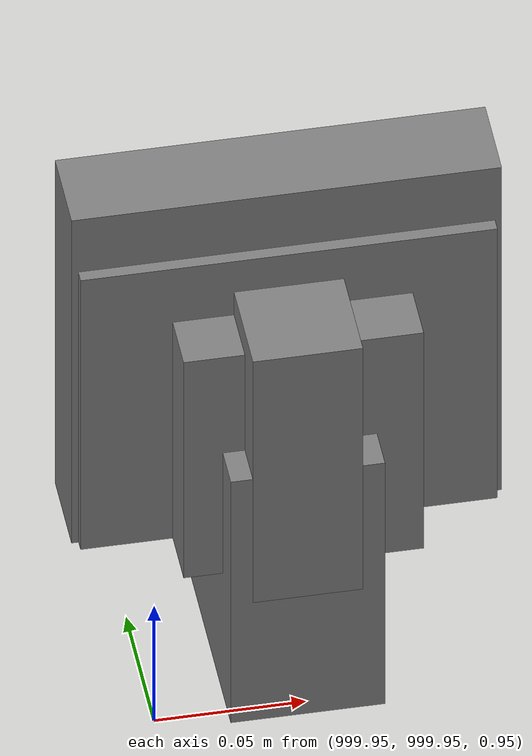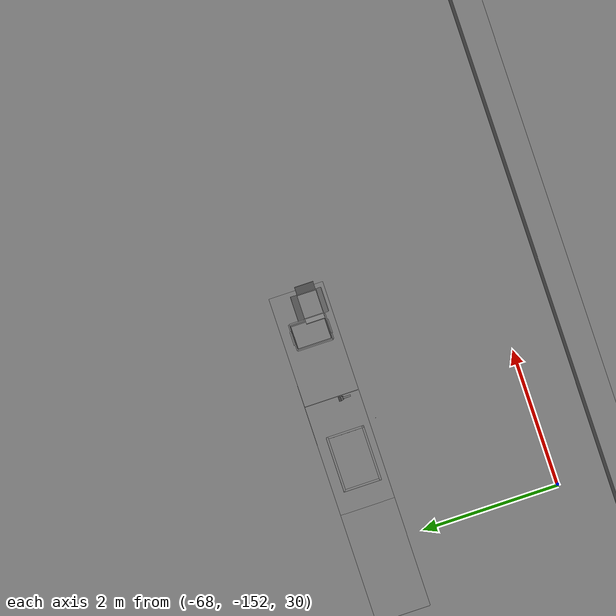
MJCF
<mujoco>
    <option gravity="0.000000000 0.000000000 -9.810000420" timestep="0.0049999999" integrator="implicitfast" density="1.225" viscosity="1.8000001e-05" noslip_iterations="10" iterations="100" sdf_iterations="50">
        <flag multiccd="disable"/>
    </option>
    <size memory="1000M"/>
    <compiler coordinate="local"/>
    <worldbody>
        <light cutoff="30" pos="0 1 1" dir="0 -1 -2"/>
        <light cutoff="30" pos="0 -1 1" dir="0 1 -2"/>
        <body pos="1000.000000000 1000.000000000 1.000000000" euler="0.000000000 0.000000000 180.000000000" name="openloong_gripper_2f85_fix_base_usda_battery_01">
            <geom contype="1" conaffinity="1" density="1000" type="box" material="" rgba="0.500000000 0.500000000 0.500000000 1.000000000" solimp="0.899999976 0.949999988 0.001000000" friction="1.000000000 0.005000000 0.000100000" solref="0.020000000 1.000000000" margin="0" condim="3" group="0" pos="-0.011123657 -0.041940309 0.101691343" quat="1.000000000 0.000000000 0.000000000 0.000000000" size="0.010800000 0.003375000 0.004725000" name="openloong_gripper_2f85_fix_base_usda_geom_DD07C409_8730_4E46_A0D1_DA8F63F7FE32"/>
            <geom contype="1" conaffinity="1" density="1000" type="box" material="" rgba="0.500000000 0.500000000 0.500000000 1.000000000" solimp="0.899999976 0.949999988 0.001000000" friction="1.000000000 0.005000000 0.000100000" solref="0.020000000 1.000000000" margin="0" condim="3" group="0" pos="-0.010876465 -0.044247437 0.047066893" quat="0.998702705 -0.050920475 0.000000000 0.000000000" size="0.009450001 0.002700000 0.024975000" name="openloong_gripper_2f85_fix_base_usda_geom_4E0CFBD3_B7D2_4523_823C_233576D2FA28"/>
            <geom contype="1" conaffinity="1" density="1000" type="box" material="" rgba="0.500000000 0.500000000 0.500000000 1.000000000" solimp="0.899999976 0.949999988 0.001000000" friction="1.000000000 0.005000000 0.000100000" solref="0.020000000 1.000000000" margin="0" condim="3" group="0" pos="-0.001235962 -0.000659180 0.047381196" quat="1.000000000 0.000000000 0.000000000 0.000000000" size="0.039420001 0.039150000 0.047250003" name="openloong_gripper_2f85_fix_base_usda_geom_FF320FCF_B8BC_4C91_B501_50D8DAC1DAE0"/>
            <geom contype="1" conaffinity="1" density="1000" type="box" material="" rgba="0.500000000 0.500000000 0.500000000 1.000000000" solimp="0.899999976 0.949999988 0.001000000" friction="1.000000000 0.005000000 0.000100000" solref="0.020000000 1.000000000" margin="0" condim="3" group="0" pos="-0.010876465 -0.039138794 0.009851727" quat="1.000000000 0.000000000 0.000000000 0.000000000" size="0.009450001 0.010800000 0.013500000" name="openloong_gripper_2f85_fix_base_usda_geom_EB332ED9_0598_40FE_82D1_E954AC19A2BB"/>
            <geom contype="1" conaffinity="1" density="1000" type="box" material="" rgba="0.500000000 0.500000000 0.500000000 1.000000000" solimp="0.899999976 0.949999988 0.001000000" friction="1.000000000 0.005000000 0.000100000" solref="0.020000000 1.000000000" margin="0" condim="3" group="0" pos="-0.010876465 -0.041528322 0.071508206" quat="1.000000000 0.000000000 0.000000000 0.000000000" size="0.009450001 0.002700000 0.027000001" name="openloong_gripper_2f85_fix_base_usda_geom_AED4947D_DBDE_4CE2_A93E_6D4E98BF6790"/>
            <freejoint name="openloong_gripper_2f85_fix_base_usda_battery_01_joint"/>
            <site size="0.005000000 0.005000000 0.005000000" rgba="0.500000000 0.500000000 0.500000000 1.000000000" pos="0.000000000 0.000000000 0.000000000" quat="0.999961913 0.008726500 0.000000000 0.000000000" group="0" type="sphere" name="openloong_gripper_2f85_fix_base_usda_battery_01site"/>
        </body>
        <body pos="1000.000000000 1000.000000000 1.000000000" euler="0.000000000 0.000000000 180.000000000" name="openloong_gripper_2f85_fix_base_usda_cpu_fan">
            <geom contype="1" conaffinity="1" density="1000" type="box" material="" rgba="0.500000000 0.500000000 0.500000000 1.000000000" solimp="0.899999976 0.949999988 0.001000000" friction="1.000000000 0.005000000 0.000100000" solref="0.020000000 1.000000000" margin="0" condim="3" group="0" pos="0.000000000 0.000000000 0.070034981" quat="0.000000000 0.000000000 0.000000000 1.000000000" size="0.070700005 0.014699999 0.070700005" name="openloong_gripper_2f85_fix_base_usda_geom_D8E798FB_4F6A_4B15_A5F4_B2E34352A89E"/>
            <freejoint name="openloong_gripper_2f85_fix_base_usda_cpu_fan_joint"/>
            <site size="0.005000000 0.005000000 0.005000000" rgba="0.500000000 0.500000000 0.500000000 1.000000000" pos="0.000000000 0.000000000 0.000000000" quat="0.999961913 0.008726535 0.000000000 0.000000000" group="0" type="sphere" name="openloong_gripper_2f85_fix_base_usda_cpu_fancsite"/>
        </body>
        <body pos="1000.000000000 1000.000000000 1.000000000" euler="0.000000000 0.000000000 180.000000000" name="openloong_gripper_2f85_fix_base_usda_wifi_box">
            <geom contype="1" conaffinity="1" density="1000" type="box" material="" rgba="0.500000000 0.500000000 0.500000000 1.000000000" solimp="0.899999976 0.949999988 0.001000000" friction="1.000000000 0.005000000 0.000100000" solref="0.020000000 1.000000000" margin="0" condim="3" group="0" pos="0.000000000 0.000000000 0.058978677" quat="0.000000000 0.000000047 0.000000000 1.000000000" size="0.068499997 0.018999999 0.059000000" name="openloong_gripper_2f85_fix_base_usda_geom_4D2803BF_B774_4149_929C_BEF37FFD9CAA"/>
            <freejoint name="openloong_gripper_2f85_fix_base_usda_wifi_box_joint"/>
            <site size="0.005000000 0.005000000 0.005000000" rgba="0.500000000 0.500000000 0.500000000 1.000000000" pos="0.000000000 0.000000000 0.000000000" quat="0.999961913 0.008726500 0.000000000 0.000000000" group="0" type="sphere" name="openloong_gripper_2f85_fix_base_usda_wifi_boxsite"/>
        </body>
        <body pos="-66.240692139 -149.008407593 31.170679092" euler="-46.629611969 5.530241489 -21.864908218" mocap="true" name="spotlight3_SpotLight"/>
        <body pos="1000.000000000 1000.000000000 1.000000000" euler="0.000011953 0.000005123 -179.999984741" name="openloong_gripper_2f85_fix_base_usda_intel_box">
            <geom contype="1" conaffinity="1" density="1000" type="box" material="" rgba="0.500000000 0.500000000 0.500000000 1.000000000" solimp="0.899999976 0.949999988 0.001000000" friction="1.000000000 0.005000000 0.000100000" solref="0.020000000 1.000000000" margin="0" condim="3" group="0" pos="0.000000000 -0.000067139 0.000082284" quat="0.707106709 0.000000225 0.000000253 0.707106650" size="0.052800003 0.025300000 0.052800003" name="openloong_gripper_2f85_fix_base_usda_geom_68595806_F9B5_4BD5_82FD_E64C7B6D798B"/>
            <freejoint name="openloong_gripper_2f85_fix_base_usda_intel_box_joint"/>
            <site size="0.005000000 0.005000000 0.005000000" rgba="0.500000000 0.500000000 0.500000000 1.000000000" pos="0.000000000 0.000000000 0.000000000" quat="0.999961913 0.008726500 0.000000000 0.000000000" group="0" type="sphere" name="openloong_gripper_2f85_fix_base_usda_intel_boxsite"/>
        </body>
        <body pos="-66.306632996 -149.626754761 31.165981293" euler="32.457775116 -66.404243469 45.504802704" mocap="true" name="spotlight5_SpotLight"/>
        <body pos="1000.000000000 999.999938965 1.000000000" euler="0.000000000 0.000000000 180.000000000" name="openloong_gripper_2f85_fix_base_usda_intelcore_i5">
            <geom contype="1" conaffinity="1" density="1000" type="box" material="" rgba="0.500000000 0.500000000 0.500000000 1.000000000" solimp="0.899999976 0.949999988 0.001000000" friction="1.000000000 0.005000000 0.000100000" solref="0.020000000 1.000000000" margin="0" condim="3" group="0" pos="0.000000000 0.000000000 0.051722717" quat="0.707106709 0.000000000 0.000000000 -0.707106769" size="0.052800000 0.018080002 0.052800000" name="openloong_gripper_2f85_fix_base_usda_geom_08F426A3_A3F5_4AF8_B73C_EE4039939F2B"/>
            <freejoint name="openloong_gripper_2f85_fix_base_usda_intelcore_i5_joint"/>
            <site size="0.005000000 0.005000000 0.005000000" rgba="0.500000000 0.500000000 0.500000000 1.000000000" pos="0.000000000 0.000000000 0.000000000" quat="0.999961913 0.008726534 0.000000000 0.000000000" group="0" type="sphere" name="openloong_gripper_2f85_fix_base_usda_intelcore_i5site"/>
        </body>
        <body pos="-66.056419373 -149.591735840 31.164400101" euler="-113.325485229 26.907726288 -41.322624207" mocap="true" name="spotlight4_SpotLight"/>
        <body pos="-64.866622925 -149.383972168 30.183746338" euler="89.999984741 89.999946594 0.000000000" name="openloong_gripper_2f85_fix_base_usda_bluebox_01">
            <geom contype="1" conaffinity="1" density="1000" type="box" material="" rgba="0.500000000 0.500000000 0.500000000 1.000000000" solimp="0.899999976 0.949999988 0.001000000" friction="1.000000000 0.005000000 0.000100000" solref="0.020000000 1.000000000" margin="0" condim="3" group="0" pos="0.276580811 0.187225342 0.000068665" quat="0.707106948 0.000077471 0.707106352 0.000077486" size="0.100000001 0.057999998 0.010000000" name="openloong_gripper_2f85_fix_base_usda_geom_75418053_8DB2_4015_BD12_A330C4B5AD81"/>
            <geom contype="1" conaffinity="1" density="1000" type="box" material="" rgba="0.500000000 0.500000000 0.500000000 1.000000000" solimp="0.899999976 0.949999988 0.001000000" friction="1.000000000 0.005000000 0.000100000" solref="0.020000000 1.000000000" margin="0" condim="3" group="0" pos="0.000000000 0.002883911 0.000000000" quat="0.999999881 0.000000000 0.000000000 0.000000000" size="0.254000008 0.003000000 0.172000006" name="openloong_gripper_2f85_fix_base_usda_geom_C758FF7B_0970_435D_B361_E59E4DE03F31"/>
            <geom contype="1" conaffinity="1" density="1000" type="box" material="" rgba="0.500000000 0.500000000 0.500000000 1.000000000" solimp="0.899999976 0.949999988 0.001000000" friction="1.000000000 0.005000000 0.000100000" solref="0.020000000 1.000000000" margin="0" condim="3" group="0" pos="0.000000000 0.124874115 0.173484802" quat="0.999796331 0.020176515 -0.000000015 0.000000030" size="0.259999990 0.119999997 0.007000000" name="openloong_gripper_2f85_fix_base_usda_geom_6914D0FD_E6D1_44B8_9A97_3057B7F9479A"/>
            <geom contype="1" conaffinity="1" density="1000" type="box" material="" rgba="0.500000000 0.500000000 0.500000000 1.000000000" solimp="0.899999976 0.949999988 0.001000000" friction="1.000000000 0.005000000 0.000100000" solref="0.020000000 1.000000000" margin="0" condim="3" group="0" pos="0.000000000 0.124874115 -0.173469543" quat="0.999796331 -0.020176545 -0.000000015 0.000000000" size="0.259999990 0.119999997 0.007000000" name="openloong_gripper_2f85_fix_base_usda_geom_7247FBB9_E863_4426_A29B_864546C2B473"/>
            <geom contype="1" conaffinity="1" density="1000" type="box" material="" rgba="0.500000000 0.500000000 0.500000000 1.000000000" solimp="0.899999976 0.949999988 0.001000000" friction="1.000000000 0.005000000 0.000100000" solref="0.020000000 1.000000000" margin="0" condim="3" group="0" pos="0.000000000 0.214008331 0.188980103" quat="0.999912977 0.013176724 0.000000015 0.000000000" size="0.259999990 0.029999999 0.012500000" name="openloong_gripper_2f85_fix_base_usda_geom_D6FA1651_B243_4BDB_B127_E226EB04F7EC"/>
            <geom contype="1" conaffinity="1" density="1000" type="box" material="" rgba="0.500000000 0.500000000 0.500000000 1.000000000" solimp="0.899999976 0.949999988 0.001000000" friction="1.000000000 0.005000000 0.000100000" solref="0.020000000 1.000000000" margin="0" condim="3" group="0" pos="-0.258361816 0.125289917 0.001876831" quat="0.702796936 -0.020792112 0.710783124 0.020769298" size="0.189999998 0.119999997 0.009000000" name="openloong_gripper_2f85_fix_base_usda_geom_96B15A1B_52C9_4232_A555_47707C33FED2"/>
            <geom contype="1" conaffinity="1" density="1000" type="box" material="" rgba="0.500000000 0.500000000 0.500000000 1.000000000" solimp="0.899999976 0.949999988 0.001000000" friction="1.000000000 0.005000000 0.000100000" solref="0.020000000 1.000000000" margin="0" condim="3" group="0" pos="0.000000000 0.214008331 -0.188980103" quat="0.999912977 -0.013176769 0.000000030 0.000000015" size="0.259999990 0.029999999 0.012500000" name="openloong_gripper_2f85_fix_base_usda_geom_EEC8B249_B46D_4090_AB61_7EA1FE236E52"/>
            <geom contype="1" conaffinity="1" density="1000" type="box" material="" rgba="0.500000000 0.500000000 0.500000000 1.000000000" solimp="0.899999976 0.949999988 0.001000000" friction="1.000000000 0.005000000 0.000100000" solref="0.020000000 1.000000000" margin="0" condim="3" group="0" pos="-0.276611328 0.187225342 0.000068665" quat="0.707106650 0.000077441 0.707106709 0.000077456" size="0.100000001 0.057999998 0.010000000" name="openloong_gripper_2f85_fix_base_usda_geom_5C6E93ED_6A30_4C47_B29F_E80CE5787D56"/>
            <geom contype="1" conaffinity="1" density="1000" type="box" material="" rgba="0.500000000 0.500000000 0.500000000 1.000000000" solimp="0.899999976 0.949999988 0.001000000" friction="1.000000000 0.005000000 0.000100000" solref="0.020000000 1.000000000" margin="0" condim="3" group="0" pos="0.258331299 0.125289917 0.001876831" quat="0.702851415 0.018856421 0.710823774 -0.019329369" size="0.189999998 0.119999997 0.009000000" name="openloong_gripper_2f85_fix_base_usda_geom_00706D29_E80D_4861_BED8_7B7AFECB4CFB"/>
            <freejoint name="openloong_gripper_2f85_fix_base_usda_bluebox_01_joint"/>
            <site size="0.005000000 0.005000000 0.005000000" rgba="0.500000000 0.500000000 0.500000000 1.000000000" pos="0.000000000 0.000000000 0.000000000" quat="0.999961913 0.008726534 0.000000000 0.000000000" group="0" type="sphere" name="openloong_gripper_2f85_fix_base_usda_bluebox_01site"/>
        </body>
        <body pos="-64.496299744 -149.491867065 30.235729218" euler="0.000000000 0.000000000 89.999946594" name="openloong_gripper_2f85_fix_base_usda_cardboardbox_01">
            <geom contype="1" conaffinity="1" density="1000" type="box" material="" rgba="0.500000000 0.500000000 0.500000000 1.000000000" solimp="0.899999976 0.949999988 0.001000000" friction="1.000000000 0.005000000 0.000100000" solref="0.020000000 1.000000000" margin="0" condim="3" group="0" pos="-0.003166199 -0.004086494 0.005052090" quat="1.000000000 0.000000000 0.000000000 0.000000000" size="0.142499998 0.177500010 0.005000000" name="openloong_gripper_2f85_fix_base_usda_geom_DE52C325_49E9_41B8_871F_017D40086F94"/>
            <geom contype="1" conaffinity="1" density="1000" type="box" material="" rgba="0.500000000 0.500000000 0.500000000 1.000000000" solimp="0.899999976 0.949999988 0.001000000" friction="1.000000000 0.005000000 0.000100000" solref="0.020000000 1.000000000" margin="0" condim="3" group="0" pos="-0.003166199 0.170316696 0.150570869" quat="1.000000000 0.000000000 0.000000000 0.000000000" size="0.142499998 0.005000000 0.149999991" name="openloong_gripper_2f85_fix_base_usda_geom_7AB2B003_119E_4CE1_A5AC_82523DD6175D"/>
            <geom contype="1" conaffinity="1" density="1000" type="box" material="" rgba="0.500000000 0.500000000 0.500000000 1.000000000" solimp="0.899999976 0.949999988 0.001000000" friction="1.000000000 0.005000000 0.000100000" solref="0.020000000 1.000000000" margin="0" condim="3" group="0" pos="-0.147399902 -0.005307198 0.150570869" quat="1.000000000 0.000000000 0.000000000 0.000000000" size="0.005000000 0.177500010 0.149999991" name="openloong_gripper_2f85_fix_base_usda_geom_4805FA81_7F9D_49AF_BC59_65D9A2D7FF99"/>
            <geom contype="1" conaffinity="1" density="1000" type="box" material="" rgba="0.500000000 0.500000000 0.500000000 1.000000000" solimp="0.899999976 0.949999988 0.001000000" friction="1.000000000 0.005000000 0.000100000" solref="0.020000000 1.000000000" margin="0" condim="3" group="0" pos="0.140275955 -0.005307198 0.150570869" quat="1.000000000 0.000000000 0.000000000 0.000000000" size="0.005000000 0.177500010 0.149999991" name="openloong_gripper_2f85_fix_base_usda_geom_9AC66ADD_F827_42F6_8537_99490C075361"/>
            <geom contype="1" conaffinity="1" density="1000" type="box" material="" rgba="0.500000000 0.500000000 0.500000000 1.000000000" solimp="0.899999976 0.949999988 0.001000000" friction="1.000000000 0.005000000 0.000100000" solref="0.020000000 1.000000000" margin="0" condim="3" group="0" pos="-0.003166199 -0.181550980 0.150570869" quat="1.000000000 0.000000000 0.000000000 0.000000000" size="0.142499998 0.005000000 0.149999991" name="openloong_gripper_2f85_fix_base_usda_geom_01F9DA42_9B44_4D63_94E2_FA538F37BE4C"/>
            <freejoint name="openloong_gripper_2f85_fix_base_usda_cardboardbox_01_joint"/>
            <site size="0.005000000 0.005000000 0.005000000" rgba="0.500000000 0.500000000 0.500000000 1.000000000" pos="0.000000000 0.000000000 0.000000000" quat="0.999961913 0.008726535 0.000000000 0.000000000" group="0" type="sphere" name="openloong_gripper_2f85_fix_base_usda_site_2ACF33C2_BFBB_487F_AC84_BCC9F1CB8DF5"/>
            <body pos="0.139160156 -0.004048347 0.301930904" euler="-179.999954224 49.383502960 179.999954224" name="openloong_gripper_2f85_fix_base_usda_A1_006">
                <geom contype="1" conaffinity="1" density="1000" type="box" material="" rgba="0.500000000 0.500000000 0.500000000 1.000000000" solimp="0.899999976 0.949999988 0.001000000" friction="1.000000000 0.005000000 0.000100000" solref="0.020000000 1.000000000" margin="0" condim="3" group="0" pos="-0.071587563 0.000009537 0.001745224" quat="0.999999881 0.000000000 0.000000000 0.000000000" size="0.071249999 0.179999992 0.002500000" name="openloong_gripper_2f85_fix_base_usda_geom_6848E844_600F_4363_8D51_6812959A80C1"/>
                <joint armature="0" stiffness="0.07" damping="0.0099999998" axis="0.000000 1.000000 0.000000" type="hinge" name="openloong_gripper_2f85_fix_base_usda_A1_006"/>
            </body>
            <body pos="-0.145902634 -0.004086494 0.301938057" euler="-180.000000000 -60.000011444 -180.000000000" name="openloong_gripper_2f85_fix_base_usda_A2_006">
                <geom contype="1" conaffinity="1" density="1000" type="box" material="" rgba="0.500000000 0.500000000 0.500000000 1.000000000" solimp="0.899999976 0.949999988 0.001000000" friction="1.000000000 0.005000000 0.000100000" solref="0.020000000 1.000000000" margin="0" condim="3" group="0" pos="0.071268082 0.000009537 0.002717972" quat="0.000002921 0.000000000 -0.000000030 0.999999881" size="0.071249999 0.179999992 0.002500000" name="openloong_gripper_2f85_fix_base_usda_geom_B325FDCF_487D_420B_9606_3C652D4DC3F2"/>
                <joint armature="0" stiffness="0.07" damping="0.0099999998" axis="0.000000 1.000000 0.000000" type="hinge" name="openloong_gripper_2f85_fix_base_usda_A2_006"/>
            </body>
            <body pos="-0.003385544 0.175991058 0.301930904" euler="-125.858116150 -0.000004561 0.000002331" name="openloong_gripper_2f85_fix_base_usda_B2_006">
                <geom contype="1" conaffinity="1" density="1000" type="box" material="" rgba="0.500000000 0.500000000 0.500000000 1.000000000" solimp="0.899999976 0.949999988 0.001000000" friction="1.000000000 0.005000000 0.000100000" solref="0.020000000 1.000000000" margin="0" condim="3" group="0" pos="0.000009537 -0.070939064 -0.002470016" quat="0.999614120 0.027776197 -0.000000015 0.000000030" size="0.137500003 0.064999998 0.005000000" name="openloong_gripper_2f85_fix_base_usda_geom_EEEB7694_3E59_4776_9D17_F5B95BD8D8D6"/>
                <joint armature="0" stiffness="0.07" damping="0.0099999998" axis="1.000000 0.000000 0.000000" type="hinge" name="openloong_gripper_2f85_fix_base_usda_B2_006"/>
            </body>
            <body pos="-0.003385544 -0.184140205 0.301938057" euler="147.805557251 0.000000000 0.000000000" name="openloong_gripper_2f85_fix_base_usda_B1_006">
                <geom contype="1" conaffinity="1" density="1000" type="box" material="" rgba="0.500000000 0.500000000 0.500000000 1.000000000" solimp="0.899999976 0.949999988 0.001000000" friction="1.000000000 0.005000000 0.000100000" solref="0.020000000 1.000000000" margin="0" condim="3" group="0" pos="-0.000028610 0.070202351 -0.002703667" quat="0.999614179 -0.027776167 0.000000000 0.000000000" size="0.137500003 0.064999998 0.005000000" name="openloong_gripper_2f85_fix_base_usda_geom_AF8C60F0_C377_4637_9303_71950DEEEB49"/>
                <joint armature="0" stiffness="0.07" damping="0.0099999998" axis="1.000000 0.000000 0.000000" type="hinge" name="openloong_gripper_2f85_fix_base_usda_B1_006"/>
            </body>
        </body>
        <body pos="-65.882858276 -149.481979370 30.229999542" euler="-64.487716675 0.000000000 0.000000000" name="openloong_gripper_2f85_fix_base_usda_Barcode">
            <geom contype="1" conaffinity="1" density="1000" type="box" material="" rgba="0.500000000 0.500000000 0.500000000 1.000000000" solimp="0.899999976 0.949999988 0.001000000" friction="1.000000000 0.005000000 0.000100000" solref="0.020000000 1.000000000" margin="0" condim="3" group="0" pos="0.000000000 0.013038635 0.001419067" quat="0.000000000 0.000000000 0.000000000 1.000000119" size="0.034000002 0.010000000 0.017999999" name="openloong_gripper_2f85_fix_base_usda_geom_46A60C34_C3A8_41AF_A803_9FE10DB4EEB6"/>
            <geom contype="1" conaffinity="1" density="1000" type="box" material="" rgba="0.500000000 0.500000000 0.500000000 1.000000000" solimp="0.899999976 0.949999988 0.001000000" friction="1.000000000 0.005000000 0.000100000" solref="0.020000000 1.000000000" margin="0" condim="3" group="0" pos="0.000000000 -0.035301208 -0.007095337" quat="0.000000000 0.000000000 -0.043619365 0.999048233" size="0.028999999 0.010000000 0.020000000" name="openloong_gripper_2f85_fix_base_usda_geom_4207059D_E8B6_4699_97DA_00C2F84A6B4B"/>
            <geom contype="1" conaffinity="1" density="1000" type="box" material="" rgba="0.500000000 0.500000000 0.500000000 1.000000000" solimp="0.899999976 0.949999988 0.001000000" friction="1.000000000 0.005000000 0.000100000" solref="0.020000000 1.000000000" margin="0" condim="3" group="0" pos="0.000000000 -0.043411255 -0.011749268" quat="0.922262907 0.386563420 0.000000000 0.000000000" size="0.026000001 0.010000000 0.020000000" name="openloong_gripper_2f85_fix_base_usda_geom_B2D479EB_CBAC_4FF4_A136_B7370C7695FE"/>
            <geom contype="1" conaffinity="1" density="1000" type="box" material="" rgba="0.500000000 0.500000000 0.500000000 1.000000000" solimp="0.899999976 0.949999988 0.001000000" friction="1.000000000 0.005000000 0.000100000" solref="0.020000000 1.000000000" margin="0" condim="3" group="0" pos="0.000000000 -0.016967773 -0.031860352" quat="0.000000000 0.000000000 0.000000000 1.000000119" size="0.008000000 0.010000000 0.013000000" name="openloong_gripper_2f85_fix_base_usda_geom_BB53977C_2EC9_450F_9F66_3C90517DD2AD"/>
            <geom contype="1" conaffinity="1" density="1000" type="box" material="" rgba="0.500000000 0.500000000 0.500000000 1.000000000" solimp="0.899999976 0.949999988 0.001000000" friction="1.000000000 0.005000000 0.000100000" solref="0.020000000 1.000000000" margin="0" condim="3" group="0" pos="0.000000000 -0.001869202 0.000312805" quat="0.953716993 0.300705761 0.000000000 0.000000000" size="0.032000002 0.010000000 0.018999999" name="openloong_gripper_2f85_fix_base_usda_geom_419F0BB8_342C_43E9_B077_76D40FE6E356"/>
            <geom contype="1" conaffinity="1" density="1000" type="box" material="" rgba="0.500000000 0.500000000 0.500000000 1.000000000" solimp="0.899999976 0.949999988 0.001000000" friction="1.000000000 0.005000000 0.000100000" solref="0.020000000 1.000000000" margin="0" condim="3" group="0" pos="0.000000000 -0.019531250 -0.003173828" quat="0.953716993 0.300705761 0.000000000 0.000000000" size="0.030999999 0.010000000 0.020000000" name="openloong_gripper_2f85_fix_base_usda_geom_135F5F40_6E3D_4B88_BFDF_EABFE7A1DA7E"/>
            <geom contype="1" conaffinity="1" density="1000" type="box" material="" rgba="0.500000000 0.500000000 0.500000000 1.000000000" solimp="0.899999976 0.949999988 0.001000000" friction="1.000000000 0.005000000 0.000100000" solref="0.020000000 1.000000000" margin="0" condim="3" group="0" pos="0.000000000 -0.035301208 -0.007095337" quat="0.953716993 0.300705761 0.000000000 0.000000000" size="0.028999999 0.010000000 0.020000000" name="openloong_gripper_2f85_fix_base_usda_geom_B8093521_EDDF_4F37_924B_A24D337CE15A"/>
            <geom contype="1" conaffinity="1" density="1000" type="box" material="" rgba="0.500000000 0.500000000 0.500000000 1.000000000" solimp="0.899999976 0.949999988 0.001000000" friction="1.000000000 0.005000000 0.000100000" solref="0.020000000 1.000000000" margin="0" condim="3" group="0" pos="0.000000000 -0.042617798 -0.071121216" quat="0.000000000 0.000000000 0.000000000 1.000000119" size="0.013000000 0.021000000 0.059999999" name="openloong_gripper_2f85_fix_base_usda_geom_9B8D780F_5B59_4820_9399_B6AB2F889723"/>
            <freejoint name="openloong_gripper_2f85_fix_base_usda_Barcode_joint"/>
            <site size="0.005000000 0.005000000 0.005000000" rgba="0.500000000 0.500000000 0.500000000 1.000000000" pos="0.000000000 0.000000000 0.000000000" quat="1.000000000 0.000000000 0.000000000 0.000000000" group="0" type="sphere" name="openloong_gripper_2f85_fix_base_usda_Barcode_site"/>
        </body>
        <body pos="-66.745018005 -149.392349243 30.184000015" euler="0.000000000 0.000000000 89.999946594" name="[22332970261386]_Basket_01">
            <geom contype="1" conaffinity="1" density="1000" type="box" material="" rgba="0.500000000 0.500000000 0.500000000 1.000000000" solimp="0.899999976 0.949999988 0.001000000" friction="1.000000000 0.005000000 0.000100000" solref="0.020000000 1.000000000" margin="0" condim="3" group="0" pos="-0.052425385 0.389207840 0.089787483" quat="0.707107008 0.000000000 0.000000000 0.707106411" size="0.014249999 0.014249999 0.059999999" name="[22332970261386]_geom_88082A3A_ECEC_48F8_897C_CA875F14740F"/>
            <geom contype="1" conaffinity="1" density="1000" type="box" material="" rgba="0.500000000 0.500000000 0.500000000 1.000000000" solimp="0.899999976 0.949999988 0.001000000" friction="1.000000000 0.005000000 0.000100000" solref="0.020000000 1.000000000" margin="0" condim="3" group="0" pos="0.264015198 -0.133043289 0.089787483" quat="0.707107008 0.000000000 0.000000000 0.707106411" size="0.014249999 0.014249999 0.059999999" name="[22332970261386]_geom_51E8171C_6C3B_4C16_9366_8F8CC655205D"/>
            <geom contype="1" conaffinity="1" density="1000" type="box" material="" rgba="0.500000000 0.500000000 0.500000000 1.000000000" solimp="0.899999976 0.949999988 0.001000000" friction="1.000000000 0.005000000 0.000100000" solref="0.020000000 1.000000000" margin="0" condim="3" group="0" pos="-0.264015198 -0.265548706 0.089793205" quat="0.707107008 0.000000000 0.000000000 0.707106411" size="0.014249999 0.014249999 0.059999999" name="[22332970261386]_geom_7F7C1E44_510C_4BBD_B636_C857216EF501"/>
            <geom contype="1" conaffinity="1" density="1000" type="box" material="" rgba="0.500000000 0.500000000 0.500000000 1.000000000" solimp="0.899999976 0.949999988 0.001000000" friction="1.000000000 0.005000000 0.000100000" solref="0.020000000 1.000000000" margin="0" condim="3" group="0" pos="-0.160263062 -0.389322281 0.089793205" quat="0.707107008 0.000000000 0.000000000 0.707106411" size="0.014249999 0.014249999 0.059999999" name="[22332970261386]_geom_9A9DE76B_BE2B_4B7D_8156_2B63749C7B6B"/>
            <geom contype="1" conaffinity="1" density="1000" type="box" material="" rgba="0.500000000 0.500000000 0.500000000 1.000000000" solimp="0.899999976 0.949999988 0.001000000" friction="1.000000000 0.005000000 0.000100000" solref="0.020000000 1.000000000" margin="0" condim="3" group="0" pos="0.162265778 -0.389322281 0.089787483" quat="0.707107008 0.000000000 0.000000000 0.707106411" size="0.014249999 0.014249999 0.059999999" name="[22332970261386]_geom_238DAEBD_397D_4FB1_9696_9BE81E0D4024"/>
            <geom contype="1" conaffinity="1" density="1000" type="box" material="" rgba="0.500000000 0.500000000 0.500000000 1.000000000" solimp="0.899999976 0.949999988 0.001000000" friction="1.000000000 0.005000000 0.000100000" solref="0.020000000 1.000000000" margin="0" condim="3" group="0" pos="0.264015198 0.389207840 0.089787483" quat="0.707107008 0.000000000 0.000000000 0.707106411" size="0.014249999 0.014249999 0.059999999" name="[22332970261386]_geom_B933FC06_0A8B_46B3_9B3F_11FDD6242F79"/>
            <geom contype="1" conaffinity="1" density="1000" type="box" material="" rgba="0.500000000 0.500000000 0.500000000 1.000000000" solimp="0.899999976 0.949999988 0.001000000" friction="1.000000000 0.005000000 0.000100000" solref="0.020000000 1.000000000" margin="0" condim="3" group="0" pos="-0.264015198 -0.133043289 0.089793205" quat="0.707107008 0.000000000 0.000000000 0.707106411" size="0.014249999 0.014249999 0.059999999" name="[22332970261386]_geom_2E206CB0_39CF_4FAF_B0AB_D3C2D084C724"/>
            <geom contype="1" conaffinity="1" density="1000" type="box" material="" rgba="0.500000000 0.500000000 0.500000000 1.000000000" solimp="0.899999976 0.949999988 0.001000000" friction="1.000000000 0.005000000 0.000100000" solref="0.020000000 1.000000000" margin="0" condim="3" group="0" pos="-0.264026642 0.269256592 0.089793205" quat="0.707107008 0.000000000 0.000000000 0.707106411" size="0.014249999 0.014249999 0.059999999" name="[22332970261386]_geom_EEF2CD51_BCD5_49ED_83BC_33C99716677A"/>
            <geom contype="1" conaffinity="1" density="1000" type="box" material="" rgba="0.500000000 0.500000000 0.500000000 1.000000000" solimp="0.899999976 0.949999988 0.001000000" friction="1.000000000 0.005000000 0.000100000" solref="0.020000000 1.000000000" margin="0" condim="3" group="0" pos="0.054462433 0.389207840 0.089787483" quat="0.707107008 0.000000000 0.000000000 0.707106411" size="0.014249999 0.014249999 0.059999999" name="[22332970261386]_geom_9CE83152_124A_4B22_937B_DE6502CC3DC1"/>
            <geom contype="1" conaffinity="1" density="1000" type="box" material="" rgba="0.500000000 0.500000000 0.500000000 1.000000000" solimp="0.899999976 0.949999988 0.001000000" friction="1.000000000 0.005000000 0.000100000" solref="0.020000000 1.000000000" margin="0" condim="3" group="0" pos="0.054462433 -0.389322281 0.089787483" quat="0.707107008 0.000000000 0.000000000 0.707106411" size="0.014249999 0.014249999 0.059999999" name="[22332970261386]_geom_3DD93CB6_8D3E_4A40_BF1F_D16175D6860F"/>
            <geom contype="1" conaffinity="1" density="1000" type="box" material="" rgba="0.500000000 0.500000000 0.500000000 1.000000000" solimp="0.899999976 0.949999988 0.001000000" friction="1.000000000 0.005000000 0.000100000" solref="0.020000000 1.000000000" margin="0" condim="3" group="0" pos="0.264015198 0.269256592 0.089793205" quat="0.707107008 0.000000000 0.000000000 0.707106411" size="0.014249999 0.014249999 0.059999999" name="[22332970261386]_geom_B9936CE4_CDB6_4589_AB44_0BE108BC0924"/>
            <geom contype="1" conaffinity="1" density="1000" type="box" material="" rgba="0.500000000 0.500000000 0.500000000 1.000000000" solimp="0.899999976 0.949999988 0.001000000" friction="1.000000000 0.005000000 0.000100000" solref="0.020000000 1.000000000" margin="0" condim="3" group="0" pos="0.264015198 -0.389322281 0.089787483" quat="0.707107008 0.000000000 0.000000000 0.707106411" size="0.014249999 0.014249999 0.059999999" name="[22332970261386]_geom_6BA1E327_FA29_4611_B6BD_1F2FB40FBF80"/>
            <geom contype="1" conaffinity="1" density="1000" type="box" material="" rgba="0.500000000 0.500000000 0.500000000 1.000000000" solimp="0.899999976 0.949999988 0.001000000" friction="1.000000000 0.005000000 0.000100000" solref="0.020000000 1.000000000" margin="0" condim="3" group="0" pos="0.000000000 0.000000000 0.015998840" quat="0.707107008 0.000000000 0.000000000 0.707106411" size="0.403499991 0.279000014 0.015750000" name="[22332970261386]_geom_15EDB7D0_67A7_4939_BA2C_A129ED181BFE"/>
            <geom contype="1" conaffinity="1" density="1000" type="box" material="" rgba="0.500000000 0.500000000 0.500000000 1.000000000" solimp="0.899999976 0.949999988 0.001000000" friction="1.000000000 0.005000000 0.000100000" solref="0.020000000 1.000000000" margin="0" condim="3" group="0" pos="0.000000000 -0.389476776 0.163619041" quat="0.707107008 0.000000000 0.000000000 0.707106411" size="0.015000000 0.277500004 0.015750000" name="[22332970261386]_geom_D035FD41_0867_49E2_A7B7_99DAC8C23E86"/>
            <geom contype="1" conaffinity="1" density="1000" type="box" material="" rgba="0.500000000 0.500000000 0.500000000 1.000000000" solimp="0.899999976 0.949999988 0.001000000" friction="1.000000000 0.005000000 0.000100000" solref="0.020000000 1.000000000" margin="0" condim="3" group="0" pos="0.162265778 0.389207840 0.089787483" quat="0.707107008 0.000000000 0.000000000 0.707106411" size="0.014249999 0.014249999 0.059999999" name="[22332970261386]_geom_3C2A42AE_F102_42B8_95E9_478DEF9CD08F"/>
            <geom contype="1" conaffinity="1" density="1000" type="box" material="" rgba="0.500000000 0.500000000 0.500000000 1.000000000" solimp="0.899999976 0.949999988 0.001000000" friction="1.000000000 0.005000000 0.000100000" solref="0.020000000 1.000000000" margin="0" condim="3" group="0" pos="0.000000000 0.389471054 0.163619041" quat="0.707107008 0.000000000 0.000000000 0.707106411" size="0.015000000 0.277500004 0.015750000" name="[22332970261386]_geom_898C1041_8447_42E2_A628_70F9D8CA2343"/>
            <geom contype="1" conaffinity="1" density="1000" type="box" material="" rgba="0.500000000 0.500000000 0.500000000 1.000000000" solimp="0.899999976 0.949999988 0.001000000" friction="1.000000000 0.005000000 0.000100000" solref="0.020000000 1.000000000" margin="0" condim="3" group="0" pos="-0.263511658 0.000000000 0.163619041" quat="0.707107008 0.000000000 0.000000000 0.707106411" size="0.403499991 0.015000000 0.015750000" name="[22332970261386]_geom_C50D600F_176E_47FC_B6C3_9EBE0E2000D5"/>
            <geom contype="1" conaffinity="1" density="1000" type="box" material="" rgba="0.500000000 0.500000000 0.500000000 1.000000000" solimp="0.899999976 0.949999988 0.001000000" friction="1.000000000 0.005000000 0.000100000" solref="0.020000000 1.000000000" margin="0" condim="3" group="0" pos="-0.264015198 0.141334534 0.089793205" quat="0.707107008 0.000000000 0.000000000 0.707106411" size="0.014249999 0.014249999 0.059999999" name="[22332970261386]_geom_4D5AEBEA_8DAB_4020_AF54_E17B9B3286AB"/>
            <geom contype="1" conaffinity="1" density="1000" type="box" material="" rgba="0.500000000 0.500000000 0.500000000 1.000000000" solimp="0.899999976 0.949999988 0.001000000" friction="1.000000000 0.005000000 0.000100000" solref="0.020000000 1.000000000" margin="0" condim="3" group="0" pos="0.264015198 -0.265548706 0.089787483" quat="0.707107008 0.000000000 0.000000000 0.707106411" size="0.014249999 0.014249999 0.059999999" name="[22332970261386]_geom_4DD22769_56D4_4AB9_9251_D062F03C5A81"/>
            <geom contype="1" conaffinity="1" density="1000" type="box" material="" rgba="0.500000000 0.500000000 0.500000000 1.000000000" solimp="0.899999976 0.949999988 0.001000000" friction="1.000000000 0.005000000 0.000100000" solref="0.020000000 1.000000000" margin="0" condim="3" group="0" pos="-0.160263062 0.389207840 0.089787483" quat="0.707107008 0.000000000 0.000000000 0.707106411" size="0.014249999 0.014249999 0.059999999" name="[22332970261386]_geom_9162C32E_0B3D_4901_B8F8_C58DF6651602"/>
            <geom contype="1" conaffinity="1" density="1000" type="box" material="" rgba="0.500000000 0.500000000 0.500000000 1.000000000" solimp="0.899999976 0.949999988 0.001000000" friction="1.000000000 0.005000000 0.000100000" solref="0.020000000 1.000000000" margin="0" condim="3" group="0" pos="-0.052425385 -0.389322281 0.089787483" quat="0.707107008 0.000000000 0.000000000 0.707106411" size="0.014249999 0.014249999 0.059999999" name="[22332970261386]_geom_83919C48_07A4_43C4_B02E_A5FDAB6BEDA1"/>
            <geom contype="1" conaffinity="1" density="1000" type="box" material="" rgba="0.500000000 0.500000000 0.500000000 1.000000000" solimp="0.899999976 0.949999988 0.001000000" friction="1.000000000 0.005000000 0.000100000" solref="0.020000000 1.000000000" margin="0" condim="3" group="0" pos="-0.264026642 -0.389322281 0.089793205" quat="0.707107008 0.000000000 0.000000000 0.707106411" size="0.014249999 0.014249999 0.059999999" name="[22332970261386]_geom_FEFA3088_D212_40BB_A824_493B433F8758"/>
            <geom contype="1" conaffinity="1" density="1000" type="box" material="" rgba="0.500000000 0.500000000 0.500000000 1.000000000" solimp="0.899999976 0.949999988 0.001000000" friction="1.000000000 0.005000000 0.000100000" solref="0.020000000 1.000000000" margin="0" condim="3" group="0" pos="0.264015198 0.141334534 0.089787483" quat="0.707107008 0.000000000 0.000000000 0.707106411" size="0.014249999 0.014249999 0.059999999" name="[22332970261386]_geom_7D80EBFC_05DC_4BB8_BD03_7FD37E2AA543"/>
            <geom contype="1" conaffinity="1" density="1000" type="box" material="" rgba="0.500000000 0.500000000 0.500000000 1.000000000" solimp="0.899999976 0.949999988 0.001000000" friction="1.000000000 0.005000000 0.000100000" solref="0.020000000 1.000000000" margin="0" condim="3" group="0" pos="-0.264015198 0.389207840 0.089793205" quat="0.707107008 0.000000000 0.000000000 0.707106411" size="0.014249999 0.014249999 0.059999999" name="[22332970261386]_geom_BDF05D8A_8257_4066_9431_55AE8CF3420D"/>
            <geom contype="1" conaffinity="1" density="1000" type="box" material="" rgba="0.500000000 0.500000000 0.500000000 1.000000000" solimp="0.899999976 0.949999988 0.001000000" friction="1.000000000 0.005000000 0.000100000" solref="0.020000000 1.000000000" margin="0" condim="3" group="0" pos="0.264015198 0.004480362 0.089787483" quat="0.707107008 0.000000000 0.000000000 0.707106411" size="0.014249999 0.014249999 0.059999999" name="[22332970261386]_geom_E24EBFCB_C31A_428A_9459_4F2131DD0BDA"/>
            <geom contype="1" conaffinity="1" density="1000" type="box" material="" rgba="0.500000000 0.500000000 0.500000000 1.000000000" solimp="0.899999976 0.949999988 0.001000000" friction="1.000000000 0.005000000 0.000100000" solref="0.020000000 1.000000000" margin="0" condim="3" group="0" pos="0.263694763 -0.000011444 0.163619041" quat="0.707107008 0.000000000 0.000000000 0.707106411" size="0.403499991 0.015000000 0.015750000" name="[22332970261386]_geom_BE73B850_B01E_4AB5_87BA_4DC380F1E609"/>
            <geom contype="1" conaffinity="1" density="1000" type="box" material="" rgba="0.500000000 0.500000000 0.500000000 1.000000000" solimp="0.899999976 0.949999988 0.001000000" friction="1.000000000 0.005000000 0.000100000" solref="0.020000000 1.000000000" margin="0" condim="3" group="0" pos="-0.264015198 0.004480362 0.089793205" quat="0.707107008 0.000000000 0.000000000 0.707106411" size="0.014249999 0.014249999 0.059999999" name="[22332970261386]_geom_4B1517C4_DD74_4E6B_BD7D_E38C364F8B44"/>
            <freejoint name="[22332970261386]_joint_93901B40_2D78_44C8_9E8F_A64A36C5A996"/>
        </body>
        <body pos="0.000000000 0.000000000 0.000000000" euler="0.000000000 0.000000000 0.000000000" name="Static Objects_Static Objects">
            <geom contype="1" conaffinity="1" density="1000" type="box" material="" rgba="0.500000000 0.500000000 0.500000000 1.000000000" solimp="0.899999976 0.949999988 0.001000000" friction="1.000000000 0.005000000 0.000100000" solref="0.020000000 1.000000000" margin="0" condim="3" group="0" pos="-67.544113159 -149.365814209 29.727830887" quat="0.500000417 0.499999970 0.499999553 0.499999970" size="0.381000012 0.319999993 0.041000001" name="Static Objects_geom_0C1FB0AC_9D9D_4B5A_9C9B_4FE5BB386524"/>
            <geom contype="1" conaffinity="1" density="1000" type="box" material="" rgba="0.500000000 0.500000000 0.500000000 1.000000000" solimp="0.899999976 0.949999988 0.001000000" friction="1.000000000 0.005000000 0.000100000" solref="0.020000000 1.000000000" margin="0" condim="3" group="0" pos="-68.239501953 -149.365814209 30.086868286" quat="0.500000417 0.499999970 0.499999553 0.499999970" size="0.370999992 0.039500002 0.745000005" name="Static Objects_geom_CA90BC07_57FC_417C_BD27_540516C205A3"/>
            <geom contype="1" conaffinity="1" density="1000" type="box" material="" rgba="0.500000000 0.500000000 0.500000000 1.000000000" solimp="0.899999976 0.949999988 0.001000000" friction="1.000000000 0.005000000 0.000100000" solref="0.020000000 1.000000000" margin="0" condim="3" group="0" pos="-68.239501953 -149.365814209 30.147235870" quat="0.500000417 0.499999970 0.499999553 0.499999970" size="0.400000006 0.022000000 0.800000012" name="Static Objects_geom_98DC0041_3530_4202_998B_AC997A0AF9A7"/>
            <geom contype="1" conaffinity="1" density="1000" type="box" material="" rgba="0.500000000 0.500000000 0.500000000 1.000000000" solimp="0.899999976 0.949999988 0.001000000" friction="1.000000000 0.005000000 0.000100000" solref="0.020000000 1.000000000" margin="0" condim="3" group="0" pos="-68.934890747 -149.365814209 29.727830887" quat="0.500000417 0.499999970 0.499999553 0.499999970" size="0.381000012 0.319999993 0.041000001" name="Static Objects_geom_E85C2EDF_8958_400C_80FF_028DD11A3399"/>
            <geom contype="1" conaffinity="1" density="1000" type="box" material="" rgba="0.500000000 0.500000000 0.500000000 1.000000000" solimp="0.899999976 0.949999988 0.001000000" friction="1.000000000 0.005000000 0.000100000" solref="0.020000000 1.000000000" margin="0" condim="3" group="0" pos="-68.239501953 -149.365814209 29.561563492" quat="0.500000417 0.499999970 0.499999553 0.499999970" size="0.020000000 0.022000000 0.660000026" name="Static Objects_geom_960D05EB_D5FA_4A4F_91C0_D72FE9B7B32F"/>
            <geom contype="1" conaffinity="1" density="1000" type="box" material="" rgba="0.500000000 0.500000000 0.500000000 1.000000000" solimp="0.899999976 0.949999988 0.001000000" friction="1.000000000 0.005000000 0.000100000" solref="0.020000000 1.000000000" margin="0" condim="3" group="0" pos="-65.945671082 -149.365814209 29.727830887" quat="0.500000417 0.499999970 0.499999553 0.499999970" size="0.381000012 0.319999993 0.041000001" name="Static Objects_geom_A9984955_1FC5_4DD1_89F9_3A32E693391A"/>
            <geom contype="1" conaffinity="1" density="1000" type="box" material="" rgba="0.500000000 0.500000000 0.500000000 1.000000000" solimp="0.899999976 0.949999988 0.001000000" friction="1.000000000 0.005000000 0.000100000" solref="0.020000000 1.000000000" margin="0" condim="3" group="0" pos="-66.641059875 -149.365814209 30.086868286" quat="0.500000417 0.499999970 0.499999553 0.499999970" size="0.370999992 0.039500002 0.745000005" name="Static Objects_geom_D55CB618_9210_4083_BFE9_0C71F3F5028B"/>
            <geom contype="1" conaffinity="1" density="1000" type="box" material="" rgba="0.500000000 0.500000000 0.500000000 1.000000000" solimp="0.899999976 0.949999988 0.001000000" friction="1.000000000 0.005000000 0.000100000" solref="0.020000000 1.000000000" margin="0" condim="3" group="0" pos="-66.641059875 -149.365814209 30.147235870" quat="0.500000417 0.499999970 0.499999553 0.499999970" size="0.400000006 0.022000000 0.800000012" name="Static Objects_geom_0560E656_D95C_4F97_A63E_008DBDEDDB62"/>
            <geom contype="1" conaffinity="1" density="1000" type="box" material="" rgba="0.500000000 0.500000000 0.500000000 1.000000000" solimp="0.899999976 0.949999988 0.001000000" friction="1.000000000 0.005000000 0.000100000" solref="0.020000000 1.000000000" margin="0" condim="3" group="0" pos="-67.336448669 -149.365814209 29.727830887" quat="0.500000417 0.499999970 0.499999553 0.499999970" size="0.381000012 0.319999993 0.041000001" name="Static Objects_geom_FD5B3B79_C543_4CC2_BD04_CF0763599B30"/>
            <geom contype="1" conaffinity="1" density="1000" type="box" material="" rgba="0.500000000 0.500000000 0.500000000 1.000000000" solimp="0.899999976 0.949999988 0.001000000" friction="1.000000000 0.005000000 0.000100000" solref="0.020000000 1.000000000" margin="0" condim="3" group="0" pos="-66.641059875 -149.365814209 29.561563492" quat="0.500000417 0.499999970 0.499999553 0.499999970" size="0.020000000 0.022000000 0.660000026" name="Static Objects_geom_8C75530A_D25F_4007_920B_191E47181EEE"/>
            <geom contype="1" conaffinity="1" density="1000" type="box" material="" rgba="0.500000000 0.500000000 0.500000000 1.000000000" solimp="0.899999976 0.949999988 0.001000000" friction="1.000000000 0.005000000 0.000100000" solref="0.020000000 1.000000000" margin="0" condim="3" group="0" pos="-64.338577271 -149.365814209 29.727830887" quat="0.500000417 0.499999970 0.499999553 0.499999970" size="0.381000012 0.319999993 0.041000001" name="Static Objects_geom_5B83756D_79B7_4014_B7FC_4742C7A11225"/>
            <geom contype="1" conaffinity="1" density="1000" type="box" material="" rgba="0.500000000 0.500000000 0.500000000 1.000000000" solimp="0.899999976 0.949999988 0.001000000" friction="1.000000000 0.005000000 0.000100000" solref="0.020000000 1.000000000" margin="0" condim="3" group="0" pos="-65.033966064 -149.365814209 30.086868286" quat="0.500000417 0.499999970 0.499999553 0.499999970" size="0.370999992 0.039500002 0.745000005" name="Static Objects_geom_2BFCE3FA_C57C_4958_81A4_C54C4F2669F3"/>
            <geom contype="1" conaffinity="1" density="1000" type="box" material="" rgba="0.500000000 0.500000000 0.500000000 1.000000000" solimp="0.899999976 0.949999988 0.001000000" friction="1.000000000 0.005000000 0.000100000" solref="0.020000000 1.000000000" margin="0" condim="3" group="0" pos="-65.033966064 -149.365814209 30.147235870" quat="0.500000417 0.499999970 0.499999553 0.499999970" size="0.400000006 0.022000000 0.800000012" name="Static Objects_geom_16D9D1F6_32F9_494A_B1F6_492C4F2A629F"/>
            <geom contype="1" conaffinity="1" density="1000" type="box" material="" rgba="0.500000000 0.500000000 0.500000000 1.000000000" solimp="0.899999976 0.949999988 0.001000000" friction="1.000000000 0.005000000 0.000100000" solref="0.020000000 1.000000000" margin="0" condim="3" group="0" pos="-65.729354858 -149.365814209 29.727830887" quat="0.500000417 0.499999970 0.499999553 0.499999970" size="0.381000012 0.319999993 0.041000001" name="Static Objects_geom_D625EBEA_EE6F_4BB3_8F1F_1611DC1FD9C9"/>
            <geom contype="1" conaffinity="1" density="1000" type="box" material="" rgba="0.500000000 0.500000000 0.500000000 1.000000000" solimp="0.899999976 0.949999988 0.001000000" friction="1.000000000 0.005000000 0.000100000" solref="0.020000000 1.000000000" margin="0" condim="3" group="0" pos="-65.033966064 -149.365814209 29.561563492" quat="0.500000417 0.499999970 0.499999553 0.499999970" size="0.020000000 0.022000000 0.660000026" name="Static Objects_geom_6A696F0F_A93D_43A8_A900_331B84EA96D3"/>
            <geom contype="1" conaffinity="1" density="1000" type="box" material="" rgba="0.500000000 0.500000000 0.500000000 1.000000000" solimp="0.899999976 0.949999988 0.001000000" friction="1.000000000 0.005000000 0.000100000" solref="0.020000000 1.000000000" margin="0" condim="3" group="0" pos="-61.754566193 -137.853729248 33.906845093" quat="0.707107067 0.000000000 0.000000000 0.707106471" size="0.759999990 0.759999990 4.500000000" name="Static Objects_geom_27FD52D1_E256_45DA_8880_F220DD1F4E94"/>
            <geom contype="1" conaffinity="1" density="1000" type="box" material="" rgba="0.500000000 0.500000000 0.500000000 1.000000000" solimp="0.899999976 0.949999988 0.001000000" friction="1.000000000 0.005000000 0.000100000" solref="0.020000000 1.000000000" margin="0" condim="3" group="0" pos="-57.511135101 -144.927108765 31.707921982" quat="1.000000000 0.000000000 0.000000000 0.000000000" size="0.200000003 8.000000000 2.299999952" name="Static Objects_geom_862E3968_FDBE_444E_AE0C_48E093DD9EE1"/>
            <geom contype="1" conaffinity="1" density="1000" type="box" material="" rgba="0.500000000 0.500000000 0.500000000 1.000000000" solimp="0.899999976 0.949999988 0.001000000" friction="1.000000000 0.005000000 0.000100000" solref="0.020000000 1.000000000" margin="0" condim="3" group="0" pos="-80.517646790 -157.574050903 31.688196182" quat="0.707107067 0.000000000 0.000000000 0.707106471" size="0.600000024 0.600000024 2.299999952" name="Static Objects_geom_9F5A1DD5_8382_40DC_8E18_9D12BA57C73C"/>
            <geom contype="1" conaffinity="1" density="1000" type="box" material="" rgba="0.500000000 0.500000000 0.500000000 1.000000000" solimp="0.899999976 0.949999988 0.001000000" friction="1.000000000 0.005000000 0.000100000" solref="0.020000000 1.000000000" margin="0" condim="3" group="0" pos="-80.711044312 -147.414932251 31.666158676" quat="1.000000000 0.000000000 0.000000000 0.000000000" size="0.200000003 10.000000000 2.299999952" name="Static Objects_geom_CC831F19_5539_469E_95E2_4F20B345122F"/>
            <geom contype="1" conaffinity="1" density="1000" type="box" material="" rgba="0.500000000 0.500000000 0.500000000 1.000000000" solimp="0.899999976 0.949999988 0.001000000" friction="1.000000000 0.005000000 0.000100000" solref="0.020000000 1.000000000" margin="0" condim="3" group="0" pos="-57.687217712 -137.434692383 31.688196182" quat="0.707107067 0.000000000 0.000000000 0.707106471" size="0.600000024 0.600000024 2.299999952" name="Static Objects_geom_4588F9A4_FA65_4DAE_A574_454EBDE819D0"/>
            <geom contype="1" conaffinity="1" density="1000" type="box" material="" rgba="0.500000000 0.500000000 0.500000000 1.000000000" solimp="0.899999976 0.949999988 0.001000000" friction="1.000000000 0.005000000 0.000100000" solref="0.020000000 1.000000000" margin="0" condim="3" group="0" pos="-69.537033081 -140.263229370 31.714921951" quat="0.707107067 0.000000000 0.000000000 0.707106471" size="0.759999990 4.500000000 2.299999952" name="Static Objects_geom_3EBA8763_6145_46F7_8494_8803F5B70DA2"/>
            <geom contype="1" conaffinity="1" density="1000" type="box" material="" rgba="0.500000000 0.500000000 0.500000000 1.000000000" solimp="0.899999976 0.949999988 0.001000000" friction="1.000000000 0.005000000 0.000100000" solref="0.020000000 1.000000000" margin="0" condim="3" group="0" pos="-80.073638916 -137.853713989 33.906845093" quat="0.707107067 0.000000000 0.000000000 0.707106471" size="0.759999990 0.759999990 4.500000000" name="Static Objects_geom_40A53C61_B63C_475D_A807_E2E01F88FF12"/>
            <geom contype="1" conaffinity="1" density="1000" type="box" material="" rgba="0.500000000 0.500000000 0.500000000 1.000000000" solimp="0.899999976 0.949999988 0.001000000" friction="1.000000000 0.005000000 0.000100000" solref="0.020000000 1.000000000" margin="0" condim="3" group="0" pos="-73.406707764 -155.734664917 31.707921982" quat="1.000000000 0.000000000 0.000000000 0.000000000" size="0.200000003 3.000000000 2.299999952" name="Static Objects_geom_61C7A634_99F0_4A5C_B298_195F700E29BD"/>
            <geom contype="1" conaffinity="1" density="1000" type="box" material="" rgba="0.500000000 0.500000000 0.500000000 1.000000000" solimp="0.899999976 0.949999988 0.001000000" friction="1.000000000 0.005000000 0.000100000" solref="0.020000000 1.000000000" margin="0" condim="3" group="0" pos="-68.497543335 -137.448257446 31.707921982" quat="0.707107067 0.000000000 0.000000000 0.707106471" size="0.200000003 14.000000000 2.299999952" name="Static Objects_geom_AC597EFF_5CF2_4194_8FAD_6F62CDE43810"/>
            <geom contype="1" conaffinity="1" density="1000" type="cylinder" material="" rgba="0.500000000 0.500000000 0.500000000 1.000000000" solimp="0.899999976 0.949999988 0.001000000" friction="1.000000000 0.005000000 0.000100000" solref="0.020000000 1.000000000" margin="0" condim="3" group="0" pos="-68.868522644 -142.134506226 31.711090088" quat="0.707107067 0.000000000 0.000000000 0.707106471" size="0.509999990 2.299999952 1.000000000" name="Static Objects_geom_505311B8_9FFA_4847_A4E1_6E564F601831"/>
            <geom contype="1" conaffinity="1" density="1000" type="plane" material="" rgba="0.500000000 0.500000000 0.500000000 1.000000000" solimp="0.899999976 0.949999988 0.001000000" friction="1.000000000 0.005000000 0.000100000" solref="0.020000000 1.000000000" margin="0" condim="3" group="0" pos="-72.873703003 -147.131927490 29.409669876" quat="1.000000000 0.000000000 0.000000000 0.000000000" size="18.000000000 14.000000000 1.000000000" name="Static Objects_geom_C1042A88_D7C9_4830_8D91_64014768BBEA"/>
            <geom contype="1" conaffinity="1" density="1000" type="box" material="" rgba="0.500000000 0.500000000 0.500000000 1.000000000" solimp="0.899999976 0.949999988 0.001000000" friction="1.000000000 0.005000000 0.000100000" solref="0.020000000 1.000000000" margin="0" condim="3" group="0" pos="-79.943580627 -157.782272339 31.707921982" quat="0.707107067 0.000000000 0.000000000 0.707106471" size="0.200000003 7.000000000 2.299999952" name="Static Objects_geom_34029972_4985_459F_B7F8_A4886813A5BB"/>
            <geom contype="1" conaffinity="1" density="1000" type="box" material="" rgba="0.500000000 0.500000000 0.500000000 1.000000000" solimp="0.899999976 0.949999988 0.001000000" friction="1.000000000 0.005000000 0.000100000" solref="0.020000000 1.000000000" margin="0" condim="3" group="0" pos="-65.421028137 -152.903442383 31.707921982" quat="0.707107067 0.000000000 0.000000000 0.707106471" size="0.200000003 7.800000191 2.299999952" name="Static Objects_geom_88245EC0_2B4B_4C09_B81A_EA5BA993467D"/>
            <geom contype="1" conaffinity="1" density="1000" type="box" material="" rgba="0.500000000 0.500000000 0.500000000 1.000000000" solimp="0.899999976 0.949999988 0.001000000" friction="1.000000000 0.005000000 0.000100000" solref="0.020000000 1.000000000" margin="0" condim="3" group="0" pos="-74.776908875 -149.964416504 31.688196182" quat="1.000000000 0.000000000 0.000000000 0.000000000" size="0.600000024 0.409999996 2.299999952" name="Static Objects_geom_47B66BA0_DEB8_4264_8DC9_733866C1B72C"/>
            <geom contype="1" conaffinity="1" density="1000" type="cylinder" material="" rgba="0.500000000 0.500000000 0.500000000 1.000000000" solimp="0.899999976 0.949999988 0.001000000" friction="1.000000000 0.005000000 0.000100000" solref="0.020000000 1.000000000" margin="0" condim="3" group="0" pos="-60.161884308 -142.134506226 31.711090088" quat="0.707107067 0.000000000 0.000000000 0.707106471" size="0.509999990 2.299999952 1.000000000" name="Static Objects_geom_3A502295_151E_444C_915D_E09503C73C9A"/>
            <geom contype="1" conaffinity="1" density="1000" type="cylinder" material="" rgba="0.500000000 0.500000000 0.500000000 1.000000000" solimp="0.899999976 0.949999988 0.001000000" friction="1.000000000 0.005000000 0.000100000" solref="0.020000000 1.000000000" margin="0" condim="3" group="0" pos="-75.382453918 -149.963455200 31.711090088" quat="0.707107067 0.000000000 0.000000000 0.707106471" size="0.409999996 2.299999952 1.000000000" name="Static Objects_geom_89AA9DC9_BC7E_4CF4_B6A3_718793C780B0"/>
            <geom contype="1" conaffinity="1" density="1000" type="cylinder" material="" rgba="0.500000000 0.500000000 0.500000000 1.000000000" solimp="0.899999976 0.949999988 0.001000000" friction="1.000000000 0.005000000 0.000100000" solref="0.020000000 1.000000000" margin="0" condim="3" group="0" pos="-74.154960632 -149.963455200 31.711090088" quat="0.707107067 0.000000000 0.000000000 0.707106471" size="0.409999996 2.299999952 1.000000000" name="Static Objects_geom_2E65524D_8190_472F_91A8_546E846DC96C"/>
            <geom contype="1" conaffinity="1" density="1000" type="cylinder" material="" rgba="0.500000000 0.500000000 0.500000000 1.000000000" solimp="0.899999976 0.949999988 0.001000000" friction="1.000000000 0.005000000 0.000100000" solref="0.020000000 1.000000000" margin="0" condim="3" group="0" pos="-77.566612244 -142.134506226 31.711090088" quat="0.707107067 0.000000000 0.000000000 0.707106471" size="0.509999990 2.299999952 1.000000000" name="Static Objects_geom_AEFEFB2C_0CDF_49B4_B0BD_0D3F92769894"/>
        </body>
        <body pos="-66.291030884 -149.869689941 29.018842697" euler="0.000000000 0.000000000 89.999946594" mocap="true" name="openloong_gripper_2f85_fix_base_usda_leftHandMocap"/>
        <body pos="-66.291030884 -149.869689941 29.018842697" euler="0.000000000 0.000000000 89.999946594" mocap="true" name="openloong_gripper_2f85_fix_base_usda_rightHandMocap"/>
        <body pos="-66.291030884 -149.869689941 30.218843460" euler="0.000000000 0.000000000 89.999946594" name="openloong_gripper_2f85_fix_base_usda_base_link">
            <geom contype="1" conaffinity="1" density="1000" type="mesh" material="" rgba="0.783999979 0.783999979 0.783999979 1.000000000" solimp="0.899999976 0.949999988 0.001000000" friction="1.000000000 0.005000000 0.000100000" solref="0.020000000 1.000000000" margin="0" condim="3" group="3" mesh="base_link" pos="0.000000000 0.000000000 0.000000000" quat="1.000000000 0.000000000 0.000000000 0.000000000" size="1.000000000 1.000000000 1.000000000" name="openloong_gripper_2f85_fix_base_usda__geom_7_5B7083C2_F3D7_4813_9A31_E48DD097BA7D"/>
            <site size="0.005000000 0.005000000 0.005000000" rgba="0.500000000 0.500000000 0.500000000 1.000000000" pos="0.000000000 0.000000000 0.000000000" quat="1.000000000 0.000000000 0.000000000 0.000000000" group="0" type="sphere" name="openloong_gripper_2f85_fix_base_usda_imu"/>
            <inertial mass="22.447001" pos="-0.005664100 -0.001336700 0.238289997" diaginertia="0.374352545 0.277180195 0.220617250" quat="0.999247074 0.035235517 -0.015086859 0.006023135"/>
            <body pos="0.000000000 0.000000000 0.299997330" euler="0.000000000 0.000000000 0.000000000" name="openloong_gripper_2f85_fix_base_usda_dummy_body">
                <geom contype="1" conaffinity="1" density="1000" type="sphere" material="" rgba="0.783999979 0.783999979 0.783999979 1.000000000" solimp="0.899999976 0.949999988 0.001000000" friction="1.000000000 0.005000000 0.000100000" solref="0.020000000 1.000000000" margin="0" condim="3" group="3" pos="0.000000000 0.000000000 0.000000000" quat="1.000000000 0.000000000 0.000000000 0.000000000" size="0.010000000 0.000000000 0.000000000" name="openloong_gripper_2f85_fix_base_usda__geom_8_C103F628_08D2_4EC5_BD1C_9110EC624627"/>
                <joint armature="0.0099999998" stiffness="0" damping="0.1" axis="0.000000 0.000000 1.000000" type="hinge" name="openloong_gripper_2f85_fix_base_usda_dummy_joint"/>
                <site size="0.010000000 0.005000000 0.005000000" rgba="0.500000000 0.500000000 0.500000000 1.000000000" pos="0.000000000 0.000000000 0.000000000" quat="1.000000000 0.000000000 0.000000000 0.000000000" group="3" type="sphere" name="openloong_gripper_2f85_fix_base_usda_dummy_site"/>
            </body>
            <body pos="0.009002686 0.000000000 0.406400681" euler="0.000000000 0.000000000 0.000000000" name="openloong_gripper_2f85_fix_base_usda_Link_head_yaw">
                <geom contype="1" conaffinity="1" density="1000" type="mesh" material="" rgba="0.783999979 0.783999979 0.783999979 1.000000000" solimp="0.899999976 0.949999988 0.001000000" friction="1.000000000 0.005000000 0.000100000" solref="0.020000000 1.000000000" margin="0" condim="3" group="3" mesh="Link_head_yaw" pos="0.000000000 0.000000000 0.000000000" quat="1.000000000 0.000000000 0.000000000 0.000000000" size="1.000000000 1.000000000 1.000000000" name="openloong_gripper_2f85_fix_base_usda__geom_10_911B461D_BEEC_465D_9340_D7FB6F9D8727"/>
                <inertial mass="0.84249002" pos="0.000000000 -0.002081400 0.044801001" diaginertia="0.000700588 0.000629000 0.000553812" quat="0.706933022 -0.015675601 0.015677100 0.706933022"/>
                <body pos="0.000000000 -0.034599304 0.048500061" euler="0.000000000 0.000000000 0.000000000" name="openloong_gripper_2f85_fix_base_usda_Link_head_pitch">
                    <geom contype="1" conaffinity="1" density="1000" type="mesh" material="" rgba="0.783999979 0.783999979 0.783999979 1.000000000" solimp="0.899999976 0.949999988 0.001000000" friction="1.000000000 0.005000000 0.000100000" solref="0.020000000 1.000000000" margin="0" condim="3" group="3" mesh="Link_head_pitch" pos="0.000000000 0.000000000 0.000000000" quat="1.000000000 0.000000000 0.000000000 0.000000000" size="1.000000000 1.000000000 1.000000000" name="openloong_gripper_2f85_fix_base_usda__geom_12_3F12F677_13B3_40E5_B47E_29A009D673FB"/>
                    <inertial mass="1.3943" pos="0.020569000 0.033004001 0.125000000" diaginertia="0.006381400 0.006289940 0.004481460" quat="0.973390222 0.008406822 0.228157058 0.019624906"/>
                    <body pos="0.000000000 0.029998779 0.000000000" euler="0.000000000 0.000000000 0.000000000" name="openloong_gripper_2f85_fix_base_usda_neck_center_body">
                        <site size="0.010000000 0.005000000 0.005000000" rgba="0.500000000 0.500000000 0.500000000 1.000000000" pos="0.000000000 0.000000000 0.000000000" quat="1.000000000 0.000000000 0.000000000 0.000000000" group="3" type="sphere" name="openloong_gripper_2f85_fix_base_usda_neck_center_site"/>
                        <body pos="0.020004272 0.000000000 0.149999619" euler="-0.000002229 39.998176575 -90.000205994" name="openloong_gripper_2f85_fix_base_usda_camera_head">
                            <site size="0.010000000 0.005000000 0.005000000" rgba="0.500000000 0.500000000 0.500000000 1.000000000" pos="0.000000000 0.000000000 0.000000000" quat="1.000000000 0.000000000 0.000000000 0.000000000" group="3" type="sphere" name="openloong_gripper_2f85_fix_base_usda_camera_head_site"/>
                        </body>
                    </body>
                </body>
            </body>
            <body pos="0.003997803 -0.161598206 0.392200470" euler="0.000000000 0.000000000 0.000000000" name="openloong_gripper_2f85_fix_base_usda_Link_arm_r_01">
                <geom contype="1" conaffinity="1" density="1000" type="mesh" material="" rgba="0.783999979 0.783999979 0.783999979 1.000000000" solimp="0.899999976 0.949999988 0.001000000" friction="1.000000000 0.005000000 0.000100000" solref="0.020000000 1.000000000" margin="0" condim="3" group="3" mesh="Link_arm_r_01" pos="0.000000000 0.000000000 0.000000000" quat="1.000000000 0.000000000 0.000000000 0.000000000" size="1.000000000 1.000000000 1.000000000" name="openloong_gripper_2f85_fix_base_usda__geom_14_0E226CF3_F3B2_4E38_9607_125C3967069A"/>
                <joint armature="0.0099999998" stiffness="0" damping="1" axis="0.000000 -1.000000 0.000000" limited="true" range="-170.000015259 170.000015259" type="hinge" name="openloong_gripper_2f85_fix_base_usda_J_arm_r_01"/>
                <inertial mass="0.75641" pos="0.004494600 -0.038293999 -0.000001874" diaginertia="0.000842990 0.000803050 0.000587120" quat="-0.000163502 0.707098067 0.000812463 0.707115054"/>
                <body pos="-0.041992188 -0.041000366 0.000000000" euler="0.000000000 0.000000000 0.000000000" name="openloong_gripper_2f85_fix_base_usda_Link_arm_r_02">
                    <geom contype="1" conaffinity="1" density="1000" type="mesh" material="" rgba="0.783999979 0.783999979 0.783999979 1.000000000" solimp="0.899999976 0.949999988 0.001000000" friction="1.000000000 0.005000000 0.000100000" solref="0.020000000 1.000000000" margin="0" condim="3" group="3" mesh="Link_arm_r_02" pos="0.000000000 0.000000000 0.000000000" quat="1.000000000 0.000000000 0.000000000 0.000000000" size="1.000000000 1.000000000 1.000000000" name="openloong_gripper_2f85_fix_base_usda__geom_16_62FE8839_8071_4AD6_856A_819E4A872A8E"/>
                    <joint armature="0.0099999998" stiffness="0" damping="1" axis="-1.000000 0.000000 0.000000" limited="true" range="-105.000244141 105.000244141" type="hinge" name="openloong_gripper_2f85_fix_base_usda_J_arm_r_02"/>
                    <inertial mass="0.98500001" pos="0.041999999 -0.067430697 0.000000000" diaginertia="0.002262690 0.001730990 0.001154020" quat="0.500000000 0.500000000 -0.500000000 0.500000000"/>
                    <body pos="0.041992188 -0.122596741 0.000000000" euler="0.000000000 0.000000000 0.000000000" name="openloong_gripper_2f85_fix_base_usda_Link_arm_r_03">
                        <geom contype="1" conaffinity="1" density="1000" type="mesh" material="" rgba="0.783999979 0.783999979 0.783999979 1.000000000" solimp="0.899999976 0.949999988 0.001000000" friction="1.000000000 0.005000000 0.000100000" solref="0.020000000 1.000000000" margin="0" condim="3" group="3" mesh="Link_arm_r_03" pos="0.000000000 0.000000000 0.000000000" quat="1.000000000 0.000000000 0.000000000 0.000000000" size="1.000000000 1.000000000 1.000000000" name="openloong_gripper_2f85_fix_base_usda__geom_18_776DCDDD_B9B9_4099_AEF1_CF897364BFA0"/>
                        <joint armature="0.0099999998" stiffness="0" damping="1" axis="0.000000 -1.000000 0.000000" limited="true" range="-170.000015259 170.000015259" type="hinge" name="openloong_gripper_2f85_fix_base_usda_J_arm_r_03"/>
                        <inertial mass="0.95899999" pos="-0.001413580 -0.164663002 0.020757901" diaginertia="0.002101340 0.002064590 0.000754802" quat="0.560480952 0.454391927 -0.443732947 0.531497955"/>
                        <body pos="0.035293579 -0.177406311 0.023998260" euler="0.000000000 0.000000000 0.000000000" name="openloong_gripper_2f85_fix_base_usda_Link_arm_r_04">
                            <geom contype="1" conaffinity="1" density="1000" type="mesh" material="" rgba="0.783999979 0.783999979 0.783999979 1.000000000" solimp="0.899999976 0.949999988 0.001000000" friction="1.000000000 0.005000000 0.000100000" solref="0.020000000 1.000000000" margin="0" condim="3" group="3" mesh="Link_arm_r_04" pos="0.000000000 0.000000000 0.000000000" quat="1.000000000 0.000000000 0.000000000 0.000000000" size="1.000000000 1.000000000 1.000000000" name="openloong_gripper_2f85_fix_base_usda__geom_20_58553868_93C1_4AB8_87FF_4093A83C1F04"/>
                            <joint armature="0.0099999998" stiffness="0" damping="1" axis="-1.000000 0.000000 0.000000" limited="true" range="0.000000000 170.000015259" type="hinge" name="openloong_gripper_2f85_fix_base_usda_J_arm_r_04"/>
                            <inertial mass="0.60000002" pos="-0.038727000 -0.060766999 -0.021003000" diaginertia="0.001092610 0.000712422 0.000645102" quat="0.327701002 0.632602990 -0.467366993 0.523443997"/>
                            <body pos="-0.035293579 -0.103492737 -0.023998260" euler="0.000000000 0.000000000 0.000000000" name="openloong_gripper_2f85_fix_base_usda_Link_arm_r_05">
                                <geom contype="1" conaffinity="1" density="1000" type="mesh" material="" rgba="0.783999979 0.783999979 0.783999979 1.000000000" solimp="0.899999976 0.949999988 0.001000000" friction="1.000000000 0.005000000 0.000100000" solref="0.020000000 1.000000000" margin="0" condim="3" group="3" mesh="Link_arm_r_05" pos="0.000000000 0.000000000 0.000000000" quat="1.000000000 0.000000000 0.000000000 0.000000000" size="1.000000000 1.000000000 1.000000000" name="openloong_gripper_2f85_fix_base_usda__geom_22_E2A8E71C_2C0E_4135_B461_29661C49D9D5"/>
                                <joint armature="0.0099999998" stiffness="0" damping="1" axis="0.000000 -1.000000 0.000000" limited="true" range="-170.000015259 170.000015259" type="hinge" name="openloong_gripper_2f85_fix_base_usda_J_arm_r_05"/>
                                <inertial mass="0.68976003" pos="0.000032712 -0.068658002 -0.000111780" diaginertia="0.002522510 0.002411100 0.000448695" quat="0.707660973 0.706543028 -0.002603360 0.002470550"/>
                                <body pos="-0.026489258 -0.196502686 0.000000000" euler="0.000000000 0.000000000 0.000000000" name="openloong_gripper_2f85_fix_base_usda_Link_arm_r_06">
                                    <geom contype="1" conaffinity="1" density="1000" type="mesh" material="" rgba="0.783999979 0.783999979 0.783999979 1.000000000" solimp="0.899999976 0.949999988 0.001000000" friction="1.000000000 0.005000000 0.000100000" solref="0.020000000 1.000000000" margin="0" condim="3" group="3" mesh="Link_arm_r_06" pos="0.000000000 0.000000000 0.000000000" quat="1.000000000 0.000000000 0.000000000 0.000000000" size="1.000000000 1.000000000 1.000000000" name="openloong_gripper_2f85_fix_base_usda__geom_24_B82DC16E_18A5_4883_9C3D_BF42D3726123"/>
                                    <joint armature="0.0099999998" stiffness="0" damping="1" axis="1.000000 0.000000 0.000000" limited="true" range="-105.000244141 105.000244141" type="hinge" name="openloong_gripper_2f85_fix_base_usda_J_arm_r_06"/>
                                    <inertial mass="0.28" pos="0.026078001 -0.000000896 0.001663700" diaginertia="0.000156930 0.000145601 0.000104979" quat="0.707080841 0.001851080 0.001883810 0.707127810"/>
                                    <body pos="0.026489258 0.000000000 0.031799316" euler="0.000000000 0.000000000 0.000000000" name="openloong_gripper_2f85_fix_base_usda_Link_arm_r_07">
                                        <geom contype="1" conaffinity="1" density="1000" type="mesh" material="" rgba="0.783999979 0.783999979 0.783999979 1.000000000" solimp="0.899999976 0.949999988 0.001000000" friction="1.000000000 0.005000000 0.000100000" solref="0.020000000 1.000000000" margin="0" condim="3" group="3" mesh="Link_arm_r_07" pos="0.000000000 0.000000000 0.000000000" quat="1.000000000 0.000000000 0.000000000 0.000000000" size="1.000000000 1.000000000 1.000000000" name="openloong_gripper_2f85_fix_base_usda__geom_26_9132B40C_A334_41F2_A99C_32647F6B434B"/>
                                        <joint armature="0.0099999998" stiffness="0" damping="1" axis="0.000000 0.000000 1.000000" limited="true" range="-60.000133514 60.000133514" type="hinge" name="openloong_gripper_2f85_fix_base_usda_J_arm_r_07"/>
                                        <inertial mass="0.61353999" pos="-0.007859000 -0.158170000 -0.027736001" diaginertia="0.003037610 0.002570910 0.000729379" quat="0.427542925 0.443532884 -0.553093910 0.560867906"/>
                                        <body pos="0.000000000 0.286994934 -0.270000458" euler="150.000350952 -0.000001649 -0.000000442" name="openloong_gripper_2f85_fix_base_usda_camera_wrist_r">
                                            <site size="0.010000000 0.005000000 0.005000000" rgba="0.500000000 0.500000000 0.500000000 1.000000000" pos="0.000000000 0.000000000 0.000000000" quat="1.000000000 0.000000000 0.000000000 0.000000000" group="3" type="sphere" name="openloong_gripper_2f85_fix_base_usda_camera_wrist_r_site"/>
                                        </body>
                                        <body pos="0.000000000 -0.220008850 -0.033002853" euler="0.000000000 0.000000000 179.999969482" name="openloong_gripper_2f85_fix_base_usda_ee_center_body_r">
                                            <site size="0.010000000 0.005000000 0.005000000" rgba="0.500000000 0.500000000 0.500000000 1.000000000" pos="0.000000000 0.000000000 0.000000000" quat="1.000000000 0.000000000 0.000000000 0.000000000" group="3" type="sphere" name="openloong_gripper_2f85_fix_base_usda_ee_center_site_r"/>
                                        </body>
                                        <body pos="0.000000000 -0.066001892 -0.031000137" euler="89.999984741 0.000000000 180.000000000" name="openloong_gripper_2f85_fix_base_usda_zbr_base_link">
                                            <geom contype="1" conaffinity="1" density="1000" type="mesh" material="" rgba="0.783999979 0.783999979 0.783999979 1.000000000" solimp="0.899999976 0.949999988 0.001000000" friction="1.000000000 0.005000000 0.000100000" solref="0.020000000 1.000000000" margin="0" condim="3" group="3" mesh="base" pos="0.000000000 0.000003815 -0.000007629" quat="1.000000000 0.000000000 0.000000000 0.000000000" size="1.000000238 1.000000238 1.000000238" name="openloong_gripper_2f85_fix_base_usda__geom_30_0BC06BAD_52B9_4259_BE97_B8F02D1878D4"/>
                                            <inertial mass="0.77744102" pos="0.000000000 -0.000027039 0.035467502" diaginertia="0.000260285 0.000225381 0.000152708" quat="0.999998808 -0.001528488 0.000000000 0.000000000"/>
                                            <body pos="-0.030609138 0.004745484 0.065696731" euler="-89.999984741 -0.000000000 0.000000000" name="openloong_gripper_2f85_fix_base_usda_r_left_driver">
                                                <geom contype="1" conaffinity="1" density="1000" type="mesh" material="" rgba="0.783999979 0.783999979 0.783999979 1.000000000" solimp="0.899999976 0.949999988 0.001000000" friction="1.000000000 0.005000000 0.000100000" solref="0.020000000 1.000000000" margin="0" condim="3" group="3" mesh="driver" pos="0.030609138 0.054901138 -0.004699708" quat="0.707106829 0.707106709 0.000000000 -0.000000000" size="1.000000238 1.000000238 1.000000238" name="openloong_gripper_2f85_fix_base_usda__geom_32_E76E6653_7579_41C3_98DA_DB149324D7FF"/>
                                                <joint armature="0.0049999999" stiffness="0" damping="0.1" axis="0.000000 0.000000 1.000000" limited="true" range="0.000000000 51.566200256" type="hinge" name="openloong_gripper_2f85_fix_base_usda_r_left_driver_joint"/>
                                                <inertial mass="0.0089956298" pos="0.000000000 0.017754700 0.001073140" diaginertia="0.000001724 0.000001609 0.000000322" quat="0.681301236 0.732003212 0.000000000 0.000000000"/>
                                                <body pos="-0.031402595 0.004524232 -0.010200503" euler="0.000000000 0.000000000 180.000000000" name="openloong_gripper_2f85_fix_base_usda_r_left_coupler">
                                                    <geom contype="1" conaffinity="1" density="1000" type="mesh" material="" rgba="0.783999979 0.783999979 0.783999979 1.000000000" solimp="0.899999976 0.949999988 0.001000000" friction="1.000000000 0.005000000 0.000100000" solref="0.020000000 1.000000000" margin="0" condim="3" group="3" mesh="coupler" pos="-0.062011734 -0.050354015 0.005500795" quat="0.707106829 -0.707106709 0.000000000 -0.000000000" size="1.000000238 1.000000238 1.000000238" name="openloong_gripper_2f85_fix_base_usda__geom_34_70F092E8_F813_4249_8A41_B259FC4CA735"/>
                                                    <inertial mass="0.0140974" pos="0.000000000 0.003012090 0.023217499" diaginertia="0.000004162 0.000003522 0.000000888" quat="0.705635548 -0.045590367 0.045590367 0.705635548"/>
                                                </body>
                                            </body>
                                            <body pos="-0.012695315 -0.012001040 0.072212234" euler="-89.999984741 -0.000000000 0.000000000" name="openloong_gripper_2f85_fix_base_usda_r_left_spring_link">
                                                <geom contype="1" conaffinity="1" density="1000" type="mesh" material="" rgba="0.783999979 0.783999979 0.783999979 1.000000000" solimp="0.899999976 0.949999988 0.001000000" friction="1.000000000 0.005000000 0.000100000" solref="0.020000000 1.000000000" margin="0" condim="3" group="3" mesh="spring_link" pos="0.012695315 0.061416641 0.012050631" quat="0.707106829 0.707106709 0.000000000 -0.000000000" size="1.000000238 1.000000238 1.000000238" name="openloong_gripper_2f85_fix_base_usda__geom_36_C2D532E4_99DE_4534_8F96_C759D5888768"/>
                                                <joint armature="0.001" stiffness="0.050000001" damping="0.00125" axis="0.000000 0.000000 1.000000" limited="true" range="-17.000000000 51.566200256" type="hinge" name="openloong_gripper_2f85_fix_base_usda_r_left_spring_link_joint"/>
                                                <inertial mass="0.0221642" pos="-0.000000009 0.018162400 0.021265799" diaginertia="0.000008969 0.000006717 0.000002639" quat="0.663403213 -0.244737089 0.244737089 0.663403213"/>
                                                <body pos="-0.038208015 -0.042503368 0.002950669" euler="180.000000000 0.000000000 -0.002185660" name="openloong_gripper_2f85_fix_base_usda_r_left_follower">
                                                    <geom contype="1" conaffinity="1" density="1000" type="mesh" material="" rgba="0.783999979 0.783999979 0.783999979 1.000000000" solimp="0.899999976 0.949999988 0.001000000" friction="1.000000000 0.005000000 0.000100000" solref="0.020000000 1.000000000" margin="0" condim="3" group="3" mesh="tongue" pos="0.050918590 -0.103920005 -0.009099962" quat="0.707106829 -0.707106709 0.000000030 0.000000030" size="1.000000238 1.000000238 1.000000238" name="openloong_gripper_2f85_fix_base_usda__geom_40_7D723827_8869_4F57_97F6_E94FD0AB5B9A"/>
                                                    <geom contype="1" conaffinity="1" density="1000" type="mesh" material="" rgba="0.783999979 0.783999979 0.783999979 1.000000000" solimp="0.899999976 0.949999988 0.001000000" friction="1.000000000 0.005000000 0.000100000" solref="0.020000000 1.000000000" margin="0" condim="3" group="3" mesh="follower" pos="0.050918590 -0.103920005 -0.009099962" quat="0.707106829 -0.707106709 0.000000030 0.000000030" size="1.000000238 1.000000238 1.000000238" name="openloong_gripper_2f85_fix_base_usda__geom_39_4FF9952C_A95E_4D8C_9923_F2D05D89D073"/>
                                                    <joint armature="0.001" stiffness="0" damping="0.1" axis="0.000000 0.000000 1.000000" limited="true" range="-49.999961853 51.566200256" type="hinge" name="openloong_gripper_2f85_fix_base_usda_r_left_follower"/>
                                                    <inertial mass="0.0125222" pos="0.000000000 -0.011046000 0.012478600" diaginertia="0.000002674 0.000002456 0.000000602" quat="0.986436546 0.164143041 0.000000000 0.000000000"/>
                                                    <body pos="-0.037765510 -0.103912376 -0.009099962" euler="-89.999984741 0.000000000 0.000004829" name="openloong_gripper_2f85_fix_base_usda_r_left_pad">
                                                        <geom contype="1" conaffinity="1" density="1000" type="box" material="" rgba="0.550000012 0.550000012 0.550000012 1.000000000" solimp="0.949999988 0.990000010 0.001000000" friction="0.699999988 0.005000000 0.000100000" solref="0.020000000 1.000000000" margin="0" condim="3" group="3" mass="1e-06" pos="0.043243419 0.000003815 0.119995147" quat="0.999999881 0.000000000 0.000000000 0.000000000" size="0.002000001 0.011000003 0.009375002" name="openloong_gripper_2f85_fix_base_usda_r_left_pad1_77326A11_55CD_41F2_AD9A_C7A604C31B37"/>
                                                        <geom contype="1" conaffinity="1" density="1000" type="box" material="" rgba="0.449999988 0.449999988 0.449999988 1.000000000" solimp="0.949999988 0.990000010 0.001000000" friction="0.600000024 0.005000000 0.000100000" solref="0.020000000 1.000000000" margin="0" condim="3" group="3" mass="1e-06" pos="0.043243419 0.000003815 0.138748199" quat="0.999999881 0.000000000 0.000000000 0.000000000" size="0.002000001 0.011000003 0.009375002" name="openloong_gripper_2f85_fix_base_usda_r_left_pad2_6B19C152_F26B_472F_B220_81567F974649"/>
                                                    </body>
                                                </body>
                                            </body>
                                            <body pos="0.030593880 -0.004753114 0.065696731" euler="89.999984741 0.000000000 180.000000000" name="openloong_gripper_2f85_fix_base_usda_r_right_driver">
                                                <geom contype="1" conaffinity="1" density="1000" type="mesh" material="" rgba="0.783999979 0.783999979 0.783999979 1.000000000" solimp="0.899999976 0.949999988 0.001000000" friction="1.000000000 0.005000000 0.000100000" solref="0.020000000 1.000000000" margin="0" condim="3" group="3" mesh="driver" pos="0.030593880 0.054901138 -0.004699708" quat="0.707106829 0.707106709 0.000000000 0.000000000" size="1.000000238 1.000000238 1.000000238" name="openloong_gripper_2f85_fix_base_usda__geom_42_BE2097DB_64F7_4E43_A5FE_8017C891AEFB"/>
                                                <joint armature="0.0049999999" stiffness="0" damping="0.1" axis="0.000000 0.000000 1.000000" limited="true" range="0.000000000 51.566200256" type="hinge" name="openloong_gripper_2f85_fix_base_usda_r_right_driver_joint"/>
                                                <inertial mass="0.0089956298" pos="0.000000000 0.017754700 0.001073140" diaginertia="0.000001724 0.000001609 0.000000322" quat="0.681301236 0.732003212 0.000000000 0.000000000"/>
                                                <body pos="-0.031417854 0.004531861 -0.010202411" euler="0.000000000 0.000000000 180.000000000" name="openloong_gripper_2f85_fix_base_usda_r_right_coupler">
                                                    <geom contype="1" conaffinity="1" density="1000" type="mesh" material="" rgba="0.783999979 0.783999979 0.783999979 1.000000000" solimp="0.899999976 0.949999988 0.001000000" friction="1.000000000 0.005000000 0.000100000" solref="0.020000000 1.000000000" margin="0" condim="3" group="3" mesh="coupler" pos="-0.062042251 -0.050376903 0.005500795" quat="0.707106829 -0.707106709 0.000000000 0.000000000" size="1.000000238 1.000000238 1.000000238" name="openloong_gripper_2f85_fix_base_usda__geom_44_6F1B1350_7C11_4C37_B642_154864CE1705"/>
                                                    <inertial mass="0.0140974" pos="0.000000000 0.003012090 0.023217499" diaginertia="0.000004162 0.000003522 0.000000888" quat="0.705635548 -0.045590367 0.045590367 0.705635548"/>
                                                </body>
                                            </body>
                                            <body pos="0.012695315 0.011997226 0.072219864" euler="89.999984741 0.000000000 180.000000000" name="openloong_gripper_2f85_fix_base_usda_r_right_spring_link">
                                                <geom contype="1" conaffinity="1" density="1000" type="mesh" material="" rgba="0.783999979 0.783999979 0.783999979 1.000000000" solimp="0.899999976 0.949999988 0.001000000" friction="1.000000000 0.005000000 0.000100000" solref="0.020000000 1.000000000" margin="0" condim="3" group="3" mesh="spring_link" pos="0.012695315 0.061424270 0.012048724" quat="0.707106829 0.707106709 0.000000000 0.000000000" size="1.000000238 1.000000238 1.000000238" name="openloong_gripper_2f85_fix_base_usda__geom_46_869441FF_E5B5_4881_9648_BB2704506740"/>
                                                <joint armature="0.001" stiffness="0.050000001" damping="0.00125" axis="0.000000 0.000000 1.000000" limited="true" range="-17.000000000 51.566200256" type="hinge" name="openloong_gripper_2f85_fix_base_usda_r_right_spring_link_joint"/>
                                                <inertial mass="0.0221642" pos="-0.000000009 0.018162400 0.021265799" diaginertia="0.000008969 0.000006717 0.000002639" quat="0.663403213 -0.244737089 0.244737089 0.663403213"/>
                                                <body pos="-0.038208015 -0.042495739 0.002950669" euler="180.000000000 0.000000000 0.000000000" name="openloong_gripper_2f85_fix_base_usda_r_right_follower">
                                                    <geom contype="1" conaffinity="1" density="1000" type="mesh" material="" rgba="0.783999979 0.783999979 0.783999979 1.000000000" solimp="0.899999976 0.949999988 0.001000000" friction="1.000000000 0.005000000 0.000100000" solref="0.020000000 1.000000000" margin="0" condim="3" group="3" mesh="follower" pos="0.050888073 -0.103927635 -0.009099962" quat="0.707106829 -0.707106709 0.000000000 0.000000000" size="1.000000238 1.000000238 1.000000238" name="openloong_gripper_2f85_fix_base_usda__geom_50_AB5C2EE4_63F4_4827_A5D7_28F25DFE410B"/>
                                                    <geom contype="1" conaffinity="1" density="1000" type="mesh" material="" rgba="0.783999979 0.783999979 0.783999979 1.000000000" solimp="0.899999976 0.949999988 0.001000000" friction="1.000000000 0.005000000 0.000100000" solref="0.020000000 1.000000000" margin="0" condim="3" group="3" mesh="tongue" pos="0.050888073 -0.103927635 -0.009099962" quat="0.707106829 -0.707106709 0.000000000 0.000000000" size="1.000000238 1.000000238 1.000000238" name="openloong_gripper_2f85_fix_base_usda__geom_49_617B9C01_5F8F_4FED_93DF_83FC9AAE3E99"/>
                                                    <joint armature="0.001" stiffness="0" damping="0.1" axis="0.000000 0.000000 1.000000" limited="true" range="-49.999961853 51.566200256" type="hinge" name="openloong_gripper_2f85_fix_base_usda_r_right_follower_joint"/>
                                                    <inertial mass="0.0125222" pos="0.000000000 -0.011046000 0.012478600" diaginertia="0.000002674 0.000002456 0.000000602" quat="0.986436546 0.164143041 0.000000000 0.000000000"/>
                                                    <body pos="-0.037811287 -0.103927635 -0.009099962" euler="-89.999984741 0.000000000 0.000000000" name="openloong_gripper_2f85_fix_base_usda_r_right_pad">
                                                        <geom contype="1" conaffinity="1" density="1000" type="box" material="" rgba="0.449999988 0.449999988 0.449999988 1.000000000" solimp="0.949999988 0.990000010 0.001000000" friction="0.600000024 0.005000000 0.000100000" solref="0.020000000 1.000000000" margin="0" condim="3" group="3" mass="1e-06" pos="0.043258678 0.000000000 0.138748199" quat="1.000000000 0.000000000 0.000000000 0.000000000" size="0.002000001 0.011000003 0.009375002" name="openloong_gripper_2f85_fix_base_usda_r_right_pad2_EBD15E20_A9EE_4501_8C51_22D12FD9EA7D"/>
                                                        <geom contype="1" conaffinity="1" density="1000" type="box" material="" rgba="0.550000012 0.550000012 0.550000012 1.000000000" solimp="0.949999988 0.990000010 0.001000000" friction="0.699999988 0.005000000 0.000100000" solref="0.020000000 1.000000000" margin="0" condim="3" group="3" mass="1e-06" pos="0.043258678 0.000003815 0.120002776" quat="1.000000000 0.000000000 0.000000000 0.000000000" size="0.002000001 0.011000003 0.009375002" name="openloong_gripper_2f85_fix_base_usda_r_right_pad1_B6BFAC1B_051E_4B76_B848_A87A29B53488"/>
                                                    </body>
                                                </body>
                                            </body>
                                        </body>
                                    </body>
                                </body>
                            </body>
                        </body>
                    </body>
                </body>
            </body>
            <body pos="0.003997803 0.161590576 0.392200470" euler="0.000000000 0.000000000 0.000000000" name="openloong_gripper_2f85_fix_base_usda_Link_arm_l_01">
                <geom contype="1" conaffinity="1" density="1000" type="mesh" material="" rgba="0.783999979 0.783999979 0.783999979 1.000000000" solimp="0.899999976 0.949999988 0.001000000" friction="1.000000000 0.005000000 0.000100000" solref="0.020000000 1.000000000" margin="0" condim="3" group="3" mesh="Link_arm_l_01" pos="0.000000000 0.000000000 0.000000000" quat="1.000000000 0.000000000 0.000000000 0.000000000" size="1.000000000 1.000000000 1.000000000" name="openloong_gripper_2f85_fix_base_usda__geom_52_309CCE19_DABE_47CD_8C85_8E42BE86FC3C"/>
                <joint armature="0.0099999998" stiffness="0" damping="1" axis="0.000000 1.000000 0.000000" limited="true" range="-170.000015259 170.000015259" type="hinge" name="openloong_gripper_2f85_fix_base_usda_J_arm_l_01"/>
                <inertial mass="0.75640601" pos="-0.004494650 0.038294200 -0.000001874" diaginertia="0.000842986 0.000803053 0.000587115" quat="-0.000812496 0.707115054 0.000163424 0.707098067"/>
                <body pos="0.042007446 0.041000366 0.000000000" euler="0.000000000 0.000000000 0.000000000" name="openloong_gripper_2f85_fix_base_usda_Link_arm_l_02">
                    <geom contype="1" conaffinity="1" density="1000" type="mesh" material="" rgba="0.783999979 0.783999979 0.783999979 1.000000000" solimp="0.899999976 0.949999988 0.001000000" friction="1.000000000 0.005000000 0.000100000" solref="0.020000000 1.000000000" margin="0" condim="3" group="3" mesh="Link_arm_l_02" pos="0.000000000 0.000000000 0.000000000" quat="1.000000000 0.000000000 0.000000000 0.000000000" size="1.000000000 1.000000000 1.000000000" name="openloong_gripper_2f85_fix_base_usda__geom_54_1C4BC1CB_D1BB_42D2_ACFF_20431885088F"/>
                    <joint armature="0.0099999998" stiffness="0" damping="1" axis="-1.000000 0.000000 0.000000" limited="true" range="-105.000244141 105.000244141" type="hinge" name="openloong_gripper_2f85_fix_base_usda_J_arm_l_02"/>
                    <inertial mass="0.98500001" pos="-0.041999999 0.067430697 0.000000000" diaginertia="0.002262690 0.001730990 0.001154020" quat="0.500000000 0.500000000 -0.500000000 0.500000000"/>
                    <body pos="-0.042007446 0.122596741 0.000000000" euler="0.000000000 0.000000000 0.000000000" name="openloong_gripper_2f85_fix_base_usda_Link_arm_l_03">
                        <geom contype="1" conaffinity="1" density="1000" type="mesh" material="" rgba="0.783999979 0.783999979 0.783999979 1.000000000" solimp="0.899999976 0.949999988 0.001000000" friction="1.000000000 0.005000000 0.000100000" solref="0.020000000 1.000000000" margin="0" condim="3" group="3" mesh="Link_arm_l_03" pos="0.000000000 0.000000000 0.000000000" quat="1.000000000 0.000000000 0.000000000 0.000000000" size="1.000000000 1.000000000 1.000000000" name="openloong_gripper_2f85_fix_base_usda__geom_56_AC3A7EEA_5E59_435C_BD5E_230FEEFD12D8"/>
                        <joint armature="0.0099999998" stiffness="0" damping="1" axis="0.000000 1.000000 0.000000" limited="true" range="-170.000015259 170.000015259" type="hinge" name="openloong_gripper_2f85_fix_base_usda_J_arm_l_03"/>
                        <inertial mass="0.95899999" pos="0.001413580 0.164663002 0.020757901" diaginertia="0.002101340 0.002064590 0.000754802" quat="0.443732947 0.531497955 -0.560480952 0.454391927"/>
                        <body pos="-0.035293579 0.177406311 0.023998260" euler="0.000000000 0.000000000 0.000000000" name="openloong_gripper_2f85_fix_base_usda_Link_arm_l_04">
                            <geom contype="1" conaffinity="1" density="1000" type="mesh" material="" rgba="0.783999979 0.783999979 0.783999979 1.000000000" solimp="0.899999976 0.949999988 0.001000000" friction="1.000000000 0.005000000 0.000100000" solref="0.020000000 1.000000000" margin="0" condim="3" group="3" mesh="Link_arm_l_04" pos="0.000000000 0.000000000 0.000000000" quat="1.000000000 0.000000000 0.000000000 0.000000000" size="1.000000000 1.000000000 1.000000000" name="openloong_gripper_2f85_fix_base_usda__geom_58_817400C4_8B51_4591_8626_0A6F22EDCD78"/>
                            <joint armature="0.0099999998" stiffness="0" damping="1" axis="1.000000 0.000000 0.000000" limited="true" range="0.000000000 170.000015259" type="hinge" name="openloong_gripper_2f85_fix_base_usda_J_arm_l_04"/>
                            <inertial mass="0.60000002" pos="0.038727000 0.060767200 -0.021003200" diaginertia="0.001092570 0.000712419 0.000645098" quat="0.467370987 0.523440003 -0.327692002 0.632607996"/>
                            <body pos="0.035293579 0.103500366 -0.023998260" euler="0.000000000 0.000000000 0.000000000" name="openloong_gripper_2f85_fix_base_usda_Link_arm_l_05">
                                <geom contype="1" conaffinity="1" density="1000" type="mesh" material="" rgba="0.783999979 0.783999979 0.783999979 1.000000000" solimp="0.899999976 0.949999988 0.001000000" friction="1.000000000 0.005000000 0.000100000" solref="0.020000000 1.000000000" margin="0" condim="3" group="3" mesh="Link_arm_l_05" pos="0.000000000 0.000000000 0.000000000" quat="1.000000000 0.000000000 0.000000000 0.000000000" size="1.000000000 1.000000000 1.000000000" name="openloong_gripper_2f85_fix_base_usda__geom_60_DC926209_B270_4246_8498_B7E64E53002B"/>
                                <joint armature="0.0099999998" stiffness="0" damping="1" axis="0.000000 1.000000 0.000000" limited="true" range="-170.000015259 170.000015259" type="hinge" name="openloong_gripper_2f85_fix_base_usda_J_arm_l_05"/>
                                <inertial mass="0.68976003" pos="-0.000032712 0.068658002 -0.000111780" diaginertia="0.002522510 0.002411100 0.000448695" quat="0.706543028 0.707660973 0.002470550 -0.002603360"/>
                                <body pos="0.026504517 0.196495056 0.000000000" euler="0.000000000 0.000000000 0.000000000" name="openloong_gripper_2f85_fix_base_usda_Link_arm_l_06">
                                    <geom contype="1" conaffinity="1" density="1000" type="mesh" material="" rgba="0.783999979 0.783999979 0.783999979 1.000000000" solimp="0.899999976 0.949999988 0.001000000" friction="1.000000000 0.005000000 0.000100000" solref="0.020000000 1.000000000" margin="0" condim="3" group="3" mesh="Link_arm_l_06" pos="0.000000000 0.000000000 0.000000000" quat="1.000000000 0.000000000 0.000000000 0.000000000" size="1.000000000 1.000000000 1.000000000" name="openloong_gripper_2f85_fix_base_usda__geom_62_CE0BCB13_DB4D_42FD_9801_F5A2C0DB90EB"/>
                                    <joint armature="0.0099999998" stiffness="0" damping="1" axis="-1.000000 0.000000 0.000000" limited="true" range="-105.000244141 105.000244141" type="hinge" name="openloong_gripper_2f85_fix_base_usda_J_arm_l_06"/>
                                    <inertial mass="0.28" pos="-0.026077701 0.000000896 0.001663730" diaginertia="0.000156927 0.000145598 0.000104981" quat="0.707080841 -0.001851280 -0.001884020 0.707127810"/>
                                    <body pos="-0.026504517 0.000000000 0.031799316" euler="0.000000000 0.000000000 0.000000000" name="openloong_gripper_2f85_fix_base_usda_Link_arm_l_07">
                                        <geom contype="1" conaffinity="1" density="1000" type="mesh" material="" rgba="0.783999979 0.783999979 0.783999979 1.000000000" solimp="0.899999976 0.949999988 0.001000000" friction="1.000000000 0.005000000 0.000100000" solref="0.020000000 1.000000000" margin="0" condim="3" group="3" mesh="Link_arm_l_07" pos="0.000000000 0.000000000 0.000000000" quat="1.000000000 0.000000000 0.000000000 0.000000000" size="1.000000000 1.000000000 1.000000000" name="openloong_gripper_2f85_fix_base_usda__geom_64_3C834C72_CEFC_437E_8A11_5B15460CBA41"/>
                                        <joint armature="0.0099999998" stiffness="0" damping="1" axis="0.000000 0.000000 1.000000" limited="true" range="-60.000133514 60.000133514" type="hinge" name="openloong_gripper_2f85_fix_base_usda_J_arm_l_07"/>
                                        <inertial mass="0.61353999" pos="-0.007787200 0.157049999 -0.027733000" diaginertia="0.003037200 0.002570420 0.000729374" quat="0.443562120 0.427539080 -0.560871124 0.553070128"/>
                                        <body pos="0.000000000 -0.286994934 -0.270000458" euler="-150.000350952 0.000001955 179.976669312" name="openloong_gripper_2f85_fix_base_usda_camera_wrist_l">
                                            <site size="0.010000000 0.005000000 0.005000000" rgba="0.500000000 0.500000000 0.500000000 1.000000000" pos="0.000000000 0.000000000 0.000000000" quat="1.000000000 0.000000000 0.000000000 0.000000000" group="3" type="sphere" name="openloong_gripper_2f85_fix_base_usda_camera_wrist_l_site"/>
                                        </body>
                                        <body pos="0.000000000 0.220008850 -0.033002853" euler="0.000000000 0.000000000 0.000000000" name="openloong_gripper_2f85_fix_base_usda_ee_center_body">
                                            <site size="0.010000000 0.005000000 0.005000000" rgba="0.500000000 0.500000000 0.500000000 1.000000000" pos="0.000000000 0.000000000 0.000000000" quat="1.000000000 0.000000000 0.000000000 0.000000000" group="3" type="sphere" name="openloong_gripper_2f85_fix_base_usda_ee_center_site"/>
                                        </body>
                                        <body pos="0.000000000 0.066009521 -0.031000137" euler="-90.000007629 0.000000000 0.000000000" name="openloong_gripper_2f85_fix_base_usda_zbll_base_link">
                                            <geom contype="1" conaffinity="1" density="1000" type="mesh" material="" rgba="0.783999979 0.783999979 0.783999979 1.000000000" solimp="0.899999976 0.949999988 0.001000000" friction="1.000000000 0.005000000 0.000100000" solref="0.020000000 1.000000000" margin="0" condim="3" group="3" mesh="base" pos="0.000000000 0.000000000 0.000000000" quat="1.000000000 0.000000000 0.000000000 0.000000000" size="1.000000000 1.000000000 1.000000000" name="openloong_gripper_2f85_fix_base_usda__geom_68_4BBF0547_D59A_49EB_8D28_626929CC113F"/>
                                            <inertial mass="0.77744102" pos="0.000000000 -0.000027039 0.035467502" diaginertia="0.000260285 0.000225381 0.000152708" quat="0.999998808 -0.001528488 0.000000000 0.000000000"/>
                                            <body pos="-0.030578613 0.004755020 0.065696716" euler="-89.999984741 0.000000000 0.000000000" name="openloong_gripper_2f85_fix_base_usda_l_left_driver">
                                                <geom contype="1" conaffinity="1" density="1000" type="mesh" material="" rgba="0.783999979 0.783999979 0.783999979 1.000000000" solimp="0.899999976 0.949999988 0.001000000" friction="1.000000000 0.005000000 0.000100000" solref="0.020000000 1.000000000" margin="0" condim="3" group="3" mesh="driver" pos="0.030609131 0.054901123 -0.004699707" quat="0.707106829 0.707106709 0.000000000 0.000000000" size="1.000000000 1.000000000 1.000000000" name="openloong_gripper_2f85_fix_base_usda__geom_70_06FFC5F7_365F_47CE_BEDF_EF203EF4E6F8"/>
                                                <joint armature="0.0049999999" stiffness="0" damping="0.1" axis="0.000000 0.000000 1.000000" limited="true" range="0.000000000 51.566200256" type="hinge" name="openloong_gripper_2f85_fix_base_usda_l_left_driver_joint"/>
                                                <inertial mass="0.0089956298" pos="0.000000000 0.017754700 0.001073140" diaginertia="0.000001724 0.000001609 0.000000322" quat="0.681301236 0.732003212 0.000000000 0.000000000"/>
                                                <body pos="-0.031402588 0.004531860 -0.010200500" euler="0.000000000 0.000000000 180.000000000" name="openloong_gripper_2f85_fix_base_usda_l_left_coupler">
                                                    <geom contype="1" conaffinity="1" density="1000" type="mesh" material="" rgba="0.783999979 0.783999979 0.783999979 1.000000000" solimp="0.899999976 0.949999988 0.001000000" friction="1.000000000 0.005000000 0.000100000" solref="0.020000000 1.000000000" margin="0" condim="3" group="3" mesh="coupler" pos="-0.062042236 -0.050369263 0.005500793" quat="0.707106829 -0.707106709 0.000000000 0.000000000" size="1.000000000 1.000000000 1.000000000" name="openloong_gripper_2f85_fix_base_usda__geom_72_DDEDD0B9_73B0_4746_A4C9_E5B9B2FBB6C9"/>
                                                    <inertial mass="0.0140974" pos="0.000000000 0.003012090 0.023217499" diaginertia="0.000004162 0.000003522 0.000000888" quat="0.705635548 -0.045590367 0.045590367 0.705635548"/>
                                                </body>
                                            </body>
                                            <body pos="-0.012680054 -0.011987686 0.072204590" euler="-89.999984741 0.000000000 0.000000000" name="openloong_gripper_2f85_fix_base_usda_l_left_spring_link">
                                                <geom contype="1" conaffinity="1" density="1000" type="mesh" material="" rgba="0.783999979 0.783999979 0.783999979 1.000000000" solimp="0.899999976 0.949999988 0.001000000" friction="1.000000000 0.005000000 0.000100000" solref="0.020000000 1.000000000" margin="0" condim="3" group="3" mesh="spring_link" pos="0.012725830 0.061431885 0.012050629" quat="0.707106829 0.707106709 0.000000000 0.000000000" size="1.000000000 1.000000000 1.000000000" name="openloong_gripper_2f85_fix_base_usda__geom_74_532C9AF7_2A4B_4630_A1AD_9DF9503496A8"/>
                                                <joint armature="0.001" stiffness="0.050000001" damping="0.00125" axis="0.000000 0.000000 1.000000" limited="true" range="-17.000000000 51.566200256" type="hinge" name="openloong_gripper_2f85_fix_base_usda_l_left_spring_link_joint"/>
                                                <inertial mass="0.0221642" pos="-0.000000009 0.018162400 0.021265799" diaginertia="0.000008969 0.000006717 0.000002639" quat="0.663403213 -0.244737089 0.244737089 0.663403213"/>
                                                <body pos="-0.038192749 -0.042495728 0.002950668" euler="180.000000000 0.000000000 -0.002185660" name="openloong_gripper_2f85_fix_base_usda_l_left_follower">
                                                    <geom contype="1" conaffinity="1" density="1000" type="mesh" material="" rgba="0.783999979 0.783999979 0.783999979 1.000000000" solimp="0.899999976 0.949999988 0.001000000" friction="1.000000000 0.005000000 0.000100000" solref="0.020000000 1.000000000" margin="0" condim="3" group="3" mesh="follower" pos="0.050933838 -0.103919983 -0.009098053" quat="0.707106829 -0.707106650 0.000000000 -0.000000030" size="1.000000000 1.000000000 1.000000000" name="openloong_gripper_2f85_fix_base_usda__geom_77_B1959884_4974_4F5B_A208_50ABA66F6DB7"/>
                                                    <geom contype="1" conaffinity="1" density="1000" type="mesh" material="" rgba="0.783999979 0.783999979 0.783999979 1.000000000" solimp="0.899999976 0.949999988 0.001000000" friction="1.000000000 0.005000000 0.000100000" solref="0.020000000 1.000000000" margin="0" condim="3" group="3" mesh="tongue" pos="0.050933838 -0.103919983 -0.009098053" quat="0.707106829 -0.707106650 0.000000000 -0.000000030" size="1.000000000 1.000000000 1.000000000" name="openloong_gripper_2f85_fix_base_usda__geom_78_D4C495CB_ECD0_4314_B66D_D7A3983F648C"/>
                                                    <joint armature="0.001" stiffness="0" damping="0.1" axis="0.000000 0.000000 1.000000" limited="true" range="-49.999961853 51.566200256" type="hinge" name="openloong_gripper_2f85_fix_base_usda_l_left_follower"/>
                                                    <inertial mass="0.0125222" pos="0.000000000 -0.011046000 0.012478600" diaginertia="0.000002674 0.000002456 0.000000602" quat="0.986436546 0.164143041 0.000000000 0.000000000"/>
                                                    <body pos="-0.037780762 -0.103919983 -0.009098053" euler="-89.999977112 0.000002415 -0.000002415" name="openloong_gripper_2f85_fix_base_usda_l_left_pad">
                                                        <geom contype="1" conaffinity="1" density="1000" type="box" material="" rgba="0.550000012 0.550000012 0.550000012 1.000000000" solimp="0.949999988 0.990000010 0.001000000" friction="0.699999988 0.005000000 0.000100000" solref="0.020000000 1.000000000" margin="0" condim="3" group="3" mass="1e-06" pos="0.043273926 0.000009537 0.119995117" quat="0.999999881 0.000000000 0.000000000 0.000000000" size="0.002000000 0.011000000 0.009375000" name="openloong_gripper_2f85_fix_base_usda_l_left_pad1_98520E3E_E3E6_4F15_9162_C2D65F28A30A"/>
                                                        <geom contype="1" conaffinity="1" density="1000" type="box" material="" rgba="0.449999988 0.449999988 0.449999988 1.000000000" solimp="0.949999988 0.990000010 0.001000000" friction="0.600000024 0.005000000 0.000100000" solref="0.020000000 1.000000000" margin="0" condim="3" group="3" mass="1e-06" pos="0.043273926 0.000017166 0.138732910" quat="0.999999881 0.000000000 0.000000000 0.000000000" size="0.002000000 0.011000000 0.009375000" name="openloong_gripper_2f85_fix_base_usda_l_left_pad2_AD0D6FC3_A0F5_4DE5_9AB3_183DDFF14490"/>
                                                    </body>
                                                </body>
                                            </body>
                                            <body pos="0.030609131 -0.004739761 0.065689087" euler="89.999984741 0.000000000 180.000000000" name="openloong_gripper_2f85_fix_base_usda_l_right_driver">
                                                <geom contype="1" conaffinity="1" density="1000" type="mesh" material="" rgba="0.783999979 0.783999979 0.783999979 1.000000000" solimp="0.899999976 0.949999988 0.001000000" friction="1.000000000 0.005000000 0.000100000" solref="0.020000000 1.000000000" margin="0" condim="3" group="3" mesh="driver" pos="0.030593872 0.054901123 -0.004697800" quat="0.707106829 0.707106709 0.000000000 0.000000000" size="1.000000000 1.000000000 1.000000000" name="openloong_gripper_2f85_fix_base_usda__geom_80_34229DEE_FA78_4C81_9589_1B3AC1AD98FA"/>
                                                <joint armature="0.0049999999" stiffness="0" damping="0.1" axis="0.000000 0.000000 1.000000" limited="true" range="0.000000000 51.566200256" type="hinge" name="openloong_gripper_2f85_fix_base_usda_l_right_driver_joint"/>
                                                <inertial mass="0.0089956298" pos="0.000000000 0.017754700 0.001073140" diaginertia="0.000001724 0.000001609 0.000000322" quat="0.681301236 0.732003212 0.000000000 0.000000000"/>
                                                <body pos="-0.031433105 0.004531860 -0.010198593" euler="0.000000000 0.000000000 180.000000000" name="openloong_gripper_2f85_fix_base_usda_l_right_coupler">
                                                    <geom contype="1" conaffinity="1" density="1000" type="mesh" material="" rgba="0.783999979 0.783999979 0.783999979 1.000000000" solimp="0.899999976 0.949999988 0.001000000" friction="1.000000000 0.005000000 0.000100000" solref="0.020000000 1.000000000" margin="0" condim="3" group="3" mesh="coupler" pos="-0.062011719 -0.050369263 0.005502701" quat="0.707106829 -0.707106709 0.000000000 0.000000000" size="1.000000000 1.000000000 1.000000000" name="openloong_gripper_2f85_fix_base_usda__geom_82_E3E7492A_6494_4758_8D39_0C5FF16198EF"/>
                                                    <inertial mass="0.0140974" pos="0.000000000 0.003012090 0.023217499" diaginertia="0.000004162 0.000003522 0.000000888" quat="0.705635548 -0.045590367 0.045590367 0.705635548"/>
                                                </body>
                                            </body>
                                            <body pos="0.012710571 0.012010574 0.072204590" euler="89.999984741 0.000000000 180.000000000" name="openloong_gripper_2f85_fix_base_usda_l_right_spring_link">
                                                <geom contype="1" conaffinity="1" density="1000" type="mesh" material="" rgba="0.783999979 0.783999979 0.783999979 1.000000000" solimp="0.899999976 0.949999988 0.001000000" friction="1.000000000 0.005000000 0.000100000" solref="0.020000000 1.000000000" margin="0" condim="3" group="3" mesh="spring_link" pos="0.012695312 0.061416626 0.012052536" quat="0.707106829 0.707106709 0.000000000 0.000000000" size="1.000000000 1.000000000 1.000000000" name="openloong_gripper_2f85_fix_base_usda__geom_84_F29935DF_CA2A_41B5_88AB_52D448D16688"/>
                                                <joint armature="0.001" stiffness="0.050000001" damping="0.00125" axis="0.000000 0.000000 1.000000" limited="true" range="-17.000000000 51.566200256" type="hinge" name="openloong_gripper_2f85_fix_base_usda_l_right_spring_link_joint"/>
                                                <inertial mass="0.0221642" pos="-0.000000009 0.018162400 0.021265799" diaginertia="0.000008969 0.000006717 0.000002639" quat="0.663403213 -0.244737089 0.244737089 0.663403213"/>
                                                <body pos="-0.038208008 -0.042503357 0.002952576" euler="180.000000000 0.000000000 0.000000000" name="openloong_gripper_2f85_fix_base_usda_l_right_follower">
                                                    <geom contype="1" conaffinity="1" density="1000" type="mesh" material="" rgba="0.783999979 0.783999979 0.783999979 1.000000000" solimp="0.899999976 0.949999988 0.001000000" friction="1.000000000 0.005000000 0.000100000" solref="0.020000000 1.000000000" margin="0" condim="3" group="3" mesh="tongue" pos="0.050903320 -0.103919983 -0.009099960" quat="0.707106829 -0.707106709 -0.000000030 -0.000000030" size="1.000000000 1.000000000 1.000000000" name="openloong_gripper_2f85_fix_base_usda__geom_87_810C0497_7627_468D_AA20_1FD68BE6F0F0"/>
                                                    <geom contype="1" conaffinity="1" density="1000" type="mesh" material="" rgba="0.783999979 0.783999979 0.783999979 1.000000000" solimp="0.899999976 0.949999988 0.001000000" friction="1.000000000 0.005000000 0.000100000" solref="0.020000000 1.000000000" margin="0" condim="3" group="3" mesh="follower" pos="0.050903320 -0.103919983 -0.009099960" quat="0.707106829 -0.707106709 -0.000000030 -0.000000030" size="1.000000000 1.000000000 1.000000000" name="openloong_gripper_2f85_fix_base_usda__geom_88_AA01C2E7_5344_4126_8372_419C89C1CE3E"/>
                                                    <joint armature="0.001" stiffness="0" damping="0.1" axis="0.000000 0.000000 1.000000" limited="true" range="-49.999961853 51.566200256" type="hinge" name="openloong_gripper_2f85_fix_base_usda_l_right_follower_joint"/>
                                                    <inertial mass="0.0125222" pos="0.000000000 -0.011046000 0.012478600" diaginertia="0.000002674 0.000002456 0.000000602" quat="0.986436546 0.164143041 0.000000000 0.000000000"/>
                                                    <body pos="-0.037796021 -0.103912354 -0.009099960" euler="-89.999984741 -0.000000000 -0.000004830" name="openloong_gripper_2f85_fix_base_usda_l_right_pad">
                                                        <geom contype="1" conaffinity="1" density="1000" type="box" material="" rgba="0.550000012 0.550000012 0.550000012 1.000000000" solimp="0.949999988 0.990000010 0.001000000" friction="0.699999988 0.005000000 0.000100000" solref="0.020000000 1.000000000" margin="0" condim="3" group="3" mass="1e-06" pos="0.043258667 0.000000000 0.119995117" quat="1.000000000 0.000000000 0.000000000 0.000000000" size="0.002000000 0.011000000 0.009375000" name="openloong_gripper_2f85_fix_base_usda_l_right_pad1_1625F908_05A1_4F1D_B505_72BA2E03ED5A"/>
                                                        <geom contype="1" conaffinity="1" density="1000" type="box" material="" rgba="0.449999988 0.449999988 0.449999988 1.000000000" solimp="0.949999988 0.990000010 0.001000000" friction="0.600000024 0.005000000 0.000100000" solref="0.020000000 1.000000000" margin="0" condim="3" group="3" mass="1e-06" pos="0.043258667 0.000000000 0.138748169" quat="1.000000000 0.000000000 0.000000000 0.000000000" size="0.002000000 0.011000000 0.009375000" name="openloong_gripper_2f85_fix_base_usda_l_right_pad2_F1E17271_D604_4874_8931_BF5D2FF38171"/>
                                                    </body>
                                                </body>
                                            </body>
                                        </body>
                                    </body>
                                </body>
                            </body>
                        </body>
                    </body>
                </body>
            </body>
            <body pos="0.000000000 -0.065246582 0.000000000" euler="0.000000000 0.000000000 0.000000000" name="openloong_gripper_2f85_fix_base_usda_Link_waist_pitch">
                <geom contype="1" conaffinity="1" density="1000" type="mesh" material="" rgba="0.783999979 0.783999979 0.783999979 1.000000000" solimp="0.899999976 0.949999988 0.001000000" friction="1.000000000 0.005000000 0.000100000" solref="0.020000000 1.000000000" margin="0" condim="3" group="3" mesh="Link_waist_pitch" pos="0.000000000 0.000000000 0.000000000" quat="1.000000000 0.000000000 0.000000000 0.000000000" size="1.000000000 1.000000000 1.000000000" name="openloong_gripper_2f85_fix_base_usda__geom_90_29597A48_9F0B_4C0A_BE6A_1484EE094746"/>
                <inertial mass="2.6963999" pos="-0.000734960 0.049924999 -0.000029695" diaginertia="0.006190620 0.005201250 0.004737120" quat="0.524125040 0.474713057 -0.522095084 0.476820052"/>
                <body pos="-0.063995361 0.065498352 0.000000000" euler="0.000000000 0.000000000 0.000000000" name="openloong_gripper_2f85_fix_base_usda_Link_waist_roll">
                    <geom contype="1" conaffinity="1" density="1000" type="mesh" material="" rgba="0.783999979 0.783999979 0.783999979 1.000000000" solimp="0.899999976 0.949999988 0.001000000" friction="1.000000000 0.005000000 0.000100000" solref="0.020000000 1.000000000" margin="0" condim="3" group="3" mesh="Link_waist_roll" pos="0.000000000 0.000000000 0.000000000" quat="1.000000000 0.000000000 0.000000000 0.000000000" size="1.000000000 1.000000000 1.000000000" name="openloong_gripper_2f85_fix_base_usda__geom_92_808941CE_4EE9_4D4C_A27A_AADF29C77C4C"/>
                    <inertial mass="2.9806001" pos="-0.003742400 -0.001000000 -0.016856000" diaginertia="0.018825000 0.017314700 0.005873970" quat="0.576995134 0.408750087 0.408750087 0.576995134"/>
                    <body pos="0.067520142 0.000000000 -0.097999573" euler="0.000000000 0.000000000 0.000000000" name="openloong_gripper_2f85_fix_base_usda_Link_waist_yaw">
                        <geom contype="1" conaffinity="1" density="1000" type="mesh" material="" rgba="0.783999979 0.783999979 0.783999979 1.000000000" solimp="0.899999976 0.949999988 0.001000000" friction="1.000000000 0.005000000 0.000100000" solref="0.020000000 1.000000000" margin="0" condim="3" group="3" mesh="Link_waist_yaw" pos="0.000000000 0.000000000 0.000000000" quat="1.000000000 0.000000000 0.000000000 0.000000000" size="1.000000000 1.000000000 1.000000000" name="openloong_gripper_2f85_fix_base_usda__geom_94_D68F5E0A_F324_4080_AA9A_877137F8BFFF"/>
                        <inertial mass="7.3587999" pos="-0.096171997 -0.001000000 -0.057836000" diaginertia="0.109522998 0.089752100 0.032765999" quat="0.571972013 0.571972013 -0.415749997 0.415749997"/>
                        <body pos="-0.087493896 -0.120002747 -0.069000244" euler="0.000000000 0.000000000 0.000000000" name="openloong_gripper_2f85_fix_base_usda_Link_hip_r_roll">
                            <geom contype="1" conaffinity="1" density="1000" type="mesh" material="" rgba="0.783999979 0.783999979 0.783999979 1.000000000" solimp="0.899999976 0.949999988 0.001000000" friction="1.000000000 0.005000000 0.000100000" solref="0.020000000 1.000000000" margin="0" condim="3" group="3" mesh="Link_hip_r_roll" pos="0.000000000 0.000000000 0.000000000" quat="1.000000000 0.000000000 0.000000000 0.000000000" size="1.000000000 1.000000000 1.000000000" name="openloong_gripper_2f85_fix_base_usda__geom_96_79939FDB_88AA_4739_B3DA_DFF5F6E068C7"/>
                            <inertial mass="2.4333999" pos="0.075724997 -0.001061600 0.016590999" diaginertia="0.004506770 0.003996270 0.003606060" quat="0.357336968 0.610613942 0.606069922 0.363510966"/>
                            <body pos="0.082229614 -0.000999451 -0.009998322" euler="0.000000000 0.000000000 0.000000000" name="openloong_gripper_2f85_fix_base_usda_Link_hip_r_yaw">
                                <geom contype="1" conaffinity="1" density="1000" type="mesh" material="" rgba="0.783999979 0.783999979 0.783999979 1.000000000" solimp="0.899999976 0.949999988 0.001000000" friction="1.000000000 0.005000000 0.000100000" solref="0.020000000 1.000000000" margin="0" condim="3" group="3" mesh="Link_hip_r_yaw" pos="0.000000000 0.000000000 0.000000000" quat="1.000000000 0.000000000 0.000000000 0.000000000" size="1.000000000 1.000000000 1.000000000" name="openloong_gripper_2f85_fix_base_usda__geom_98_810CC992_3E35_4B68_876E_61343181A0AE"/>
                                <inertial mass="3.4303" pos="-0.000000031 -0.007135600 -0.100630000" diaginertia="0.008090100 0.007736500 0.006631600" quat="0.706536055 0.028403703 -0.028403703 0.706536055"/>
                                <body pos="0.000000000 0.036750793 -0.105501175" euler="0.000000000 0.000000000 0.000000000" name="openloong_gripper_2f85_fix_base_usda_Link_hip_r_pitch">
                                    <geom contype="1" conaffinity="1" density="1000" type="mesh" material="" rgba="0.783999979 0.783999979 0.783999979 1.000000000" solimp="0.899999976 0.949999988 0.001000000" friction="1.000000000 0.005000000 0.000100000" solref="0.020000000 1.000000000" margin="0" condim="3" group="3" mesh="Link_hip_r_pitch" pos="0.000000000 0.000000000 0.000000000" quat="1.000000000 0.000000000 0.000000000 0.000000000" size="1.000000000 1.000000000 1.000000000" name="openloong_gripper_2f85_fix_base_usda__geom_100_C89404C8_47C5_4ED9_A8CE_EFCE38A954FD"/>
                                    <inertial mass="5.2378001" pos="0.001085600 -0.054970000 -0.145349994" diaginertia="0.043490201 0.037812300 0.015138500" quat="0.999495864 -0.015916798 0.013696698 0.023812896"/>
                                    <body pos="0.000000000 -0.011253357 -0.400001526" euler="0.000000000 0.000000000 0.000000000" name="openloong_gripper_2f85_fix_base_usda_Link_knee_r_pitch">
                                        <geom contype="1" conaffinity="1" density="1000" type="mesh" material="" rgba="0.783999979 0.783999979 0.783999979 1.000000000" solimp="0.899999976 0.949999988 0.001000000" friction="1.000000000 0.005000000 0.000100000" solref="0.020000000 1.000000000" margin="0" condim="3" group="3" mesh="Link_knee_r_pitch" pos="0.000000000 0.000000000 0.000000000" quat="1.000000000 0.000000000 0.000000000 0.000000000" size="1.000000000 1.000000000 1.000000000" name="openloong_gripper_2f85_fix_base_usda__geom_102_E6BABAA5_6766_4E71_86EA_FB90586DC7FB"/>
                                        <inertial mass="2.9775" pos="-0.009642500 0.000002934 -0.136010006" diaginertia="0.024215899 0.023851801 0.002284610" quat="0.782037616 -0.003061678 0.016178992 0.623013675"/>
                                        <body pos="0.000000000 0.000000000 -0.386999130" euler="0.000000000 0.000000000 0.000000000" name="openloong_gripper_2f85_fix_base_usda_Link_ankle_r_pitch">
                                            <geom contype="1" conaffinity="1" density="1000" type="mesh" material="" rgba="0.783999979 0.783999979 0.783999979 1.000000000" solimp="0.899999976 0.949999988 0.001000000" friction="1.000000000 0.005000000 0.000100000" solref="0.020000000 1.000000000" margin="0" condim="3" group="3" mesh="Link_ankle_r_pitch" pos="0.000000000 0.000000000 0.000000000" quat="1.000000000 0.000000000 0.000000000 0.000000000" size="1.000000000 1.000000000 1.000000000" name="openloong_gripper_2f85_fix_base_usda__geom_104_323FEE05_D3B2_4C92_93E0_00E556D6BC2F"/>
                                            <inertial mass="0.10145" pos="-0.000000000 -0.000000127 -0.000000025" diaginertia="0.000027175 0.000026565 0.000006112" quat="0.707106829 0.707106829 0.000000000 0.000000000"/>
                                            <body pos="0.000000000 0.000000000 0.000000000" euler="0.000000000 0.000000000 0.000000000" name="openloong_gripper_2f85_fix_base_usda_Link_ankle_r_roll">
                                                <geom contype="1" conaffinity="1" density="1000" type="box" material="" rgba="1.000000000 0.000000000 0.000000000 0.000000000" solimp="0.899999976 0.949999988 0.001000000" friction="1.000000000 0.005000000 0.000100000" solref="0.020000000 1.000000000" margin="0" condim="3" group="3" pos="0.047515869 0.000083923 -0.026544571" quat="1.000000000 0.000000000 0.000000000 0.000000000" size="0.122500002 0.039999999 0.043499999" name="openloong_gripper_2f85_fix_base_usda__geom_106_1E6F31AB_ED56_403F_B40A_5C4F2AA3B185"/>
                                                <site size="0.123000003 0.041000001 0.044000000" rgba="0.000000000 1.000000000 0.000000000 0.000000000" pos="0.047504615 0.000082667 -0.026545310" quat="1.000000000 0.000000000 0.000000000 0.000000000" group="3" type="box" name="openloong_gripper_2f85_fix_base_usda_rf-tc"/>
                                                <inertial mass="0.75229001" pos="0.041078001 -0.000000089 -0.043908998" diaginertia="0.003659370 0.003646500 0.000416828" quat="0.000000000 0.677034914 0.000000000 0.735950947"/>
                                            </body>
                                        </body>
                                    </body>
                                </body>
                            </body>
                        </body>
                        <body pos="-0.087493896 0.120002747 -0.069000244" euler="0.000000000 0.000000000 0.000000000" name="openloong_gripper_2f85_fix_base_usda_Link_hip_l_roll">
                            <geom contype="1" conaffinity="1" density="1000" type="mesh" material="" rgba="0.783999979 0.783999979 0.783999979 1.000000000" solimp="0.899999976 0.949999988 0.001000000" friction="1.000000000 0.005000000 0.000100000" solref="0.020000000 1.000000000" margin="0" condim="3" group="3" mesh="Link_hip_l_roll" pos="0.000000000 0.000000000 0.000000000" quat="1.000000000 0.000000000 0.000000000 0.000000000" size="1.000000000 1.000000000 1.000000000" name="openloong_gripper_2f85_fix_base_usda__geom_108_83C07B43_762C_4B5E_AE50_3C13117B590A"/>
                            <inertial mass="2.4333999" pos="0.075724997 -0.000938430 0.016590999" diaginertia="0.004257030 0.003974770 0.003377790" quat="0.411751240 0.573205352 0.583885372 0.401216239"/>
                            <body pos="0.082229614 -0.000999451 -0.009998322" euler="0.000000000 0.000000000 0.000000000" name="openloong_gripper_2f85_fix_base_usda_Link_hip_l_yaw">
                                <geom contype="1" conaffinity="1" density="1000" type="mesh" material="" rgba="0.783999979 0.783999979 0.783999979 1.000000000" solimp="0.899999976 0.949999988 0.001000000" friction="1.000000000 0.005000000 0.000100000" solref="0.020000000 1.000000000" margin="0" condim="3" group="3" mesh="Link_hip_l_yaw" pos="0.000000000 0.000000000 0.000000000" quat="1.000000000 0.000000000 0.000000000 0.000000000" size="1.000000000 1.000000000 1.000000000" name="openloong_gripper_2f85_fix_base_usda__geom_110_9D5B1ED9_9A61_4506_B45A_1D01D72E5DF9"/>
                                <inertial mass="3.4303999" pos="-0.000000032 0.007135800 -0.100630000" diaginertia="0.008090100 0.007736500 0.006631500" quat="0.706536174 -0.028401807 0.028401807 0.706536174"/>
                                <body pos="0.000000000 -0.036758423 -0.105501175" euler="0.000000000 0.000000000 0.000000000" name="openloong_gripper_2f85_fix_base_usda_Link_hip_l_pitch">
                                    <geom contype="1" conaffinity="1" density="1000" type="mesh" material="" rgba="0.783999979 0.783999979 0.783999979 1.000000000" solimp="0.899999976 0.949999988 0.001000000" friction="1.000000000 0.005000000 0.000100000" solref="0.020000000 1.000000000" margin="0" condim="3" group="3" mesh="Link_hip_l_pitch" pos="0.000000000 0.000000000 0.000000000" quat="1.000000000 0.000000000 0.000000000 0.000000000" size="1.000000000 1.000000000 1.000000000" name="openloong_gripper_2f85_fix_base_usda__geom_112_FA58E793_A254_4CF5_AC16_6FB817CA996A"/>
                                    <inertial mass="5.2378001" pos="0.001085600 0.054970000 -0.145349994" diaginertia="0.043490201 0.037812300 0.015138500" quat="0.999495745 0.015916597 0.013696796 -0.023821594"/>
                                    <body pos="0.000000000 0.011260986 -0.400001526" euler="0.000000000 0.000000000 0.000000000" name="openloong_gripper_2f85_fix_base_usda_Link_knee_l_pitch">
                                        <geom contype="1" conaffinity="1" density="1000" type="mesh" material="" rgba="0.783999979 0.783999979 0.783999979 1.000000000" solimp="0.899999976 0.949999988 0.001000000" friction="1.000000000 0.005000000 0.000100000" solref="0.020000000 1.000000000" margin="0" condim="3" group="3" mesh="Link_knee_l_pitch" pos="0.000000000 0.000000000 0.000000000" quat="1.000000000 0.000000000 0.000000000 0.000000000" size="1.000000000 1.000000000 1.000000000" name="openloong_gripper_2f85_fix_base_usda__geom_114_27F09070_BFEB_4D71_87EE_48F47C131332"/>
                                        <inertial mass="2.9775" pos="-0.009642500 -0.000002868 -0.136010006" diaginertia="0.024214899 0.023850800 0.002284610" quat="0.623014212 0.016178306 -0.003060011 0.782037318"/>
                                        <body pos="0.000000000 0.000000000 -0.386999130" euler="0.000000000 0.000000000 0.000000000" name="openloong_gripper_2f85_fix_base_usda_Link_ankle_l_pitch">
                                            <geom contype="1" conaffinity="1" density="1000" type="mesh" material="" rgba="0.783999979 0.783999979 0.783999979 1.000000000" solimp="0.899999976 0.949999988 0.001000000" friction="1.000000000 0.005000000 0.000100000" solref="0.020000000 1.000000000" margin="0" condim="3" group="3" mesh="Link_ankle_l_pitch" pos="0.000000000 0.000000000 0.000000000" quat="1.000000000 0.000000000 0.000000000 0.000000000" size="1.000000000 1.000000000 1.000000000" name="openloong_gripper_2f85_fix_base_usda__geom_116_30A55A0E_59C2_4C00_8E78_B88E66972C40"/>
                                            <inertial mass="0.10145" pos="-0.000000000 0.000000127 0.000000067" diaginertia="0.000027175 0.000026565 0.000006112" quat="0.707106829 0.707106829 0.000000000 0.000000000"/>
                                            <body pos="0.000000000 0.000000000 0.000000000" euler="0.000000000 0.000000000 0.000000000" name="openloong_gripper_2f85_fix_base_usda_Link_ankle_l_roll">
                                                <geom contype="1" conaffinity="1" density="1000" type="box" material="" rgba="1.000000000 0.000000000 0.000000000 0.000000000" solimp="0.899999976 0.949999988 0.001000000" friction="1.000000000 0.005000000 0.000100000" solref="0.020000000 1.000000000" margin="0" condim="3" group="3" pos="0.047515869 0.001220703 -0.027221680" quat="1.000000000 0.000000000 0.000000000 0.000000000" size="0.122500002 0.040199999 0.044199999" name="openloong_gripper_2f85_fix_base_usda__geom_118_B0EF8E6B_2446_4052_B9C9_BB761602CB03"/>
                                                <site size="0.123000003 0.041000001 0.045000002" rgba="0.000000000 1.000000000 0.000000000 0.000000000" pos="0.047499999 0.001220864 -0.027223988" quat="1.000000000 0.000000000 0.000000000 0.000000000" group="3" type="box" name="openloong_gripper_2f85_fix_base_usda_lf-tc"/>
                                                <inertial mass="0.75228798" pos="0.041076999 -0.000000029 -0.043908998" diaginertia="0.003659370 0.003646500 0.000416828" quat="0.000000000 0.677034914 0.000000000 0.735950947"/>
                                            </body>
                                        </body>
                                    </body>
                                </body>
                            </body>
                        </body>
                    </body>
                </body>
            </body>
        </body>
    </worldbody>
    <tendon>
        <fixed name="openloong_gripper_2f85_fix_base_usda_l_split">
            <joint joint="openloong_gripper_2f85_fix_base_usda_l_right_driver_joint" coef="0.48500001"/>
            <joint joint="openloong_gripper_2f85_fix_base_usda_l_left_driver_joint" coef="0.48500001"/>
        </fixed>
        <fixed name="openloong_gripper_2f85_fix_base_usda_r_split">
            <joint joint="openloong_gripper_2f85_fix_base_usda_r_right_driver_joint" coef="0.48500001"/>
            <joint joint="openloong_gripper_2f85_fix_base_usda_r_left_driver_joint" coef="0.48500001"/>
        </fixed>
    </tendon>
    <actuator>
        <position ctrllimited="true" ctrlrange="-2.96706 2.96706" forcelimited="true" forcerange="-80 80" joint="openloong_gripper_2f85_fix_base_usda_J_arm_l_01" kp="200" kv="20" name="openloong_gripper_2f85_fix_base_usda_P_arm_l_01"/>
        <position ctrllimited="true" ctrlrange="-1.8326 1.8326" forcelimited="true" forcerange="-80 80" joint="openloong_gripper_2f85_fix_base_usda_J_arm_l_02" kp="200" kv="20" name="openloong_gripper_2f85_fix_base_usda_P_arm_l_02"/>
        <position ctrllimited="true" ctrlrange="-2.96706 2.96706" forcelimited="true" forcerange="-48 48" joint="openloong_gripper_2f85_fix_base_usda_J_arm_l_03" kp="200" kv="20" name="openloong_gripper_2f85_fix_base_usda_P_arm_l_03"/>
        <position ctrllimited="true" ctrlrange="0 2.96706" forcelimited="true" forcerange="-48 48" joint="openloong_gripper_2f85_fix_base_usda_J_arm_l_04" kp="200" kv="20" name="openloong_gripper_2f85_fix_base_usda_P_arm_l_04"/>
        <position ctrllimited="true" ctrlrange="-2.96706 2.96706" forcelimited="true" forcerange="-12.4 12.4" joint="openloong_gripper_2f85_fix_base_usda_J_arm_l_05" kp="200" kv="20" name="openloong_gripper_2f85_fix_base_usda_P_arm_l_05"/>
        <position ctrllimited="true" ctrlrange="-1.8326 1.8326" forcelimited="true" forcerange="-12.4 12.4" joint="openloong_gripper_2f85_fix_base_usda_J_arm_l_06" kp="200" kv="20" name="openloong_gripper_2f85_fix_base_usda_P_arm_l_06"/>
        <position ctrllimited="true" ctrlrange="-1.0472 1.0472" forcelimited="true" forcerange="-12.4 12.4" joint="openloong_gripper_2f85_fix_base_usda_J_arm_l_07" kp="200" kv="20" name="openloong_gripper_2f85_fix_base_usda_P_arm_l_07"/>
        <motor ctrllimited="true" ctrlrange="-80 80" gear="1" joint="openloong_gripper_2f85_fix_base_usda_J_arm_l_01" name="openloong_gripper_2f85_fix_base_usda_M_arm_l_01"/>
        <motor ctrllimited="true" ctrlrange="-80 80" gear="1" joint="openloong_gripper_2f85_fix_base_usda_J_arm_l_02" name="openloong_gripper_2f85_fix_base_usda_M_arm_l_02"/>
        <motor ctrllimited="true" ctrlrange="-48 48" gear="1" joint="openloong_gripper_2f85_fix_base_usda_J_arm_l_03" name="openloong_gripper_2f85_fix_base_usda_M_arm_l_03"/>
        <motor ctrllimited="true" ctrlrange="-48 48" gear="1" joint="openloong_gripper_2f85_fix_base_usda_J_arm_l_04" name="openloong_gripper_2f85_fix_base_usda_M_arm_l_04"/>
        <motor ctrllimited="true" ctrlrange="-12.4 12.4" gear="1" joint="openloong_gripper_2f85_fix_base_usda_J_arm_l_05" name="openloong_gripper_2f85_fix_base_usda_M_arm_l_05"/>
        <motor ctrllimited="true" ctrlrange="-12.4 12.4" gear="1" joint="openloong_gripper_2f85_fix_base_usda_J_arm_l_06" name="openloong_gripper_2f85_fix_base_usda_M_arm_l_06"/>
        <motor ctrllimited="true" ctrlrange="-12.4 12.4" gear="1" joint="openloong_gripper_2f85_fix_base_usda_J_arm_l_07" name="openloong_gripper_2f85_fix_base_usda_M_arm_l_07"/>
        <position ctrllimited="true" ctrlrange="-2.96706 2.96706" forcelimited="true" forcerange="-80 80" joint="openloong_gripper_2f85_fix_base_usda_J_arm_r_01" kp="200" kv="20" name="openloong_gripper_2f85_fix_base_usda_P_arm_r_01"/>
        <position ctrllimited="true" ctrlrange="-1.8326 1.8326" forcelimited="true" forcerange="-80 80" joint="openloong_gripper_2f85_fix_base_usda_J_arm_r_02" kp="200" kv="20" name="openloong_gripper_2f85_fix_base_usda_P_arm_r_02"/>
        <position ctrllimited="true" ctrlrange="-2.96706 2.96706" forcelimited="true" forcerange="-48 48" joint="openloong_gripper_2f85_fix_base_usda_J_arm_r_03" kp="200" kv="20" name="openloong_gripper_2f85_fix_base_usda_P_arm_r_03"/>
        <position ctrllimited="true" ctrlrange="0 2.96706" forcelimited="true" forcerange="-48 48" joint="openloong_gripper_2f85_fix_base_usda_J_arm_r_04" kp="200" kv="20" name="openloong_gripper_2f85_fix_base_usda_P_arm_r_04"/>
        <position ctrllimited="true" ctrlrange="-2.96706 2.96706" forcelimited="true" forcerange="-12.4 12.4" joint="openloong_gripper_2f85_fix_base_usda_J_arm_r_05" kp="200" kv="20" name="openloong_gripper_2f85_fix_base_usda_P_arm_r_05"/>
        <position ctrllimited="true" ctrlrange="-1.8326 1.8326" forcelimited="true" forcerange="-12.4 12.4" joint="openloong_gripper_2f85_fix_base_usda_J_arm_r_06" kp="200" kv="20" name="openloong_gripper_2f85_fix_base_usda_P_arm_r_06"/>
        <position ctrllimited="true" ctrlrange="-1.0472 1.0472" forcelimited="true" forcerange="-12.4 12.4" joint="openloong_gripper_2f85_fix_base_usda_J_arm_r_07" kp="200" kv="20" name="openloong_gripper_2f85_fix_base_usda_P_arm_r_07"/>
        <motor ctrllimited="true" ctrlrange="-80 80" gear="1" joint="openloong_gripper_2f85_fix_base_usda_J_arm_r_01" name="openloong_gripper_2f85_fix_base_usda_M_arm_r_01"/>
        <motor ctrllimited="true" ctrlrange="-80 80" gear="1" joint="openloong_gripper_2f85_fix_base_usda_J_arm_r_02" name="openloong_gripper_2f85_fix_base_usda_M_arm_r_02"/>
        <motor ctrllimited="true" ctrlrange="-48 48" gear="1" joint="openloong_gripper_2f85_fix_base_usda_J_arm_r_03" name="openloong_gripper_2f85_fix_base_usda_M_arm_r_03"/>
        <motor ctrllimited="true" ctrlrange="-48 48" gear="1" joint="openloong_gripper_2f85_fix_base_usda_J_arm_r_04" name="openloong_gripper_2f85_fix_base_usda_M_arm_r_04"/>
        <motor ctrllimited="true" ctrlrange="-12.4 12.4" gear="1" joint="openloong_gripper_2f85_fix_base_usda_J_arm_r_05" name="openloong_gripper_2f85_fix_base_usda_M_arm_r_05"/>
        <motor ctrllimited="true" ctrlrange="-12.4 12.4" gear="1" joint="openloong_gripper_2f85_fix_base_usda_J_arm_r_06" name="openloong_gripper_2f85_fix_base_usda_M_arm_r_06"/>
        <motor ctrllimited="true" ctrlrange="-12.4 12.4" gear="1" joint="openloong_gripper_2f85_fix_base_usda_J_arm_r_07" name="openloong_gripper_2f85_fix_base_usda_M_arm_r_07"/>
        <general biasprm="0 -100 -10" biastype="affine" ctrlrange="0 255" forcerange="-5 5" gainprm="0.3137255 0 0" name="openloong_gripper_2f85_fix_base_usda_l_fingers_actuator" tendon="openloong_gripper_2f85_fix_base_usda_l_split"/>
        <general biasprm="0 -100 -10" biastype="affine" ctrlrange="0 255" forcerange="-5 5" gainprm="0.3137255 0 0" name="openloong_gripper_2f85_fix_base_usda_r_fingers_actuator" tendon="openloong_gripper_2f85_fix_base_usda_r_split"/>
    </actuator>
    <contact>
        <exclude body1="openloong_gripper_2f85_fix_base_usda_base_link" body2="openloong_gripper_2f85_fix_base_usda_Link_head_yaw"/>
        <exclude body1="openloong_gripper_2f85_fix_base_usda_base_link" body2="openloong_gripper_2f85_fix_base_usda_dummy_body"/>
        <exclude body1="openloong_gripper_2f85_fix_base_usda_base_link" body2="openloong_gripper_2f85_fix_base_usda_Link_waist_roll"/>
        <exclude body1="openloong_gripper_2f85_fix_base_usda_base_link" body2="openloong_gripper_2f85_fix_base_usda_Link_arm_r_01"/>
        <exclude body1="openloong_gripper_2f85_fix_base_usda_base_link" body2="openloong_gripper_2f85_fix_base_usda_Link_waist_pitch"/>
        <exclude body1="openloong_gripper_2f85_fix_base_usda_base_link" body2="openloong_gripper_2f85_fix_base_usda_Link_head_pitch"/>
        <exclude body1="openloong_gripper_2f85_fix_base_usda_base_link" body2="openloong_gripper_2f85_fix_base_usda_Link_arm_l_01"/>
        <exclude body1="openloong_gripper_2f85_fix_base_usda_Link_arm_l_01" body2="openloong_gripper_2f85_fix_base_usda_Link_arm_l_02"/>
        <exclude body1="openloong_gripper_2f85_fix_base_usda_Link_arm_l_02" body2="openloong_gripper_2f85_fix_base_usda_Link_arm_l_03"/>
        <exclude body1="openloong_gripper_2f85_fix_base_usda_Link_arm_l_03" body2="openloong_gripper_2f85_fix_base_usda_Link_arm_l_04"/>
        <exclude body1="openloong_gripper_2f85_fix_base_usda_Link_arm_l_04" body2="openloong_gripper_2f85_fix_base_usda_Link_arm_l_05"/>
        <exclude body1="openloong_gripper_2f85_fix_base_usda_Link_arm_l_05" body2="openloong_gripper_2f85_fix_base_usda_Link_arm_l_06"/>
        <exclude body1="openloong_gripper_2f85_fix_base_usda_Link_arm_l_05" body2="openloong_gripper_2f85_fix_base_usda_Link_arm_l_07"/>
        <exclude body1="openloong_gripper_2f85_fix_base_usda_Link_arm_l_06" body2="openloong_gripper_2f85_fix_base_usda_Link_arm_l_07"/>
        <exclude body1="openloong_gripper_2f85_fix_base_usda_zbll_base_link" body2="openloong_gripper_2f85_fix_base_usda_l_left_driver"/>
        <exclude body1="openloong_gripper_2f85_fix_base_usda_zbll_base_link" body2="openloong_gripper_2f85_fix_base_usda_l_right_spring_link"/>
        <exclude body1="openloong_gripper_2f85_fix_base_usda_zbll_base_link" body2="openloong_gripper_2f85_fix_base_usda_l_left_spring_link"/>
        <exclude body1="openloong_gripper_2f85_fix_base_usda_zbll_base_link" body2="openloong_gripper_2f85_fix_base_usda_l_right_driver"/>
        <exclude body1="openloong_gripper_2f85_fix_base_usda_l_left_coupler" body2="openloong_gripper_2f85_fix_base_usda_l_left_follower"/>
        <exclude body1="openloong_gripper_2f85_fix_base_usda_l_right_coupler" body2="openloong_gripper_2f85_fix_base_usda_l_right_follower"/>
        <exclude body1="openloong_gripper_2f85_fix_base_usda_Link_waist_pitch" body2="openloong_gripper_2f85_fix_base_usda_Link_waist_roll"/>
        <exclude body1="openloong_gripper_2f85_fix_base_usda_Link_waist_roll" body2="openloong_gripper_2f85_fix_base_usda_Link_waist_yaw"/>
        <exclude body1="openloong_gripper_2f85_fix_base_usda_Link_waist_yaw" body2="openloong_gripper_2f85_fix_base_usda_Link_hip_r_yaw"/>
        <exclude body1="openloong_gripper_2f85_fix_base_usda_Link_waist_yaw" body2="openloong_gripper_2f85_fix_base_usda_Link_hip_r_roll"/>
        <exclude body1="openloong_gripper_2f85_fix_base_usda_Link_waist_yaw" body2="openloong_gripper_2f85_fix_base_usda_Link_hip_l_pitch"/>
        <exclude body1="openloong_gripper_2f85_fix_base_usda_Link_waist_yaw" body2="openloong_gripper_2f85_fix_base_usda_Link_hip_l_yaw"/>
        <exclude body1="openloong_gripper_2f85_fix_base_usda_Link_waist_yaw" body2="openloong_gripper_2f85_fix_base_usda_Link_hip_r_pitch"/>
        <exclude body1="openloong_gripper_2f85_fix_base_usda_Link_waist_yaw" body2="openloong_gripper_2f85_fix_base_usda_Link_hip_l_roll"/>
        <exclude body1="openloong_gripper_2f85_fix_base_usda_Link_hip_r_roll" body2="openloong_gripper_2f85_fix_base_usda_Link_hip_r_yaw"/>
        <exclude body1="openloong_gripper_2f85_fix_base_usda_Link_hip_r_yaw" body2="openloong_gripper_2f85_fix_base_usda_Link_hip_r_pitch"/>
        <exclude body1="openloong_gripper_2f85_fix_base_usda_Link_hip_r_pitch" body2="openloong_gripper_2f85_fix_base_usda_Link_knee_r_pitch"/>
        <exclude body1="openloong_gripper_2f85_fix_base_usda_Link_knee_r_pitch" body2="openloong_gripper_2f85_fix_base_usda_Link_ankle_r_roll"/>
        <exclude body1="openloong_gripper_2f85_fix_base_usda_Link_knee_r_pitch" body2="openloong_gripper_2f85_fix_base_usda_Link_ankle_r_pitch"/>
        <exclude body1="openloong_gripper_2f85_fix_base_usda_Link_ankle_r_pitch" body2="openloong_gripper_2f85_fix_base_usda_Link_ankle_r_roll"/>
        <exclude body1="openloong_gripper_2f85_fix_base_usda_Link_hip_l_roll" body2="openloong_gripper_2f85_fix_base_usda_Link_hip_l_yaw"/>
        <exclude body1="openloong_gripper_2f85_fix_base_usda_Link_hip_l_yaw" body2="openloong_gripper_2f85_fix_base_usda_Link_hip_l_pitch"/>
        <exclude body1="openloong_gripper_2f85_fix_base_usda_Link_hip_l_pitch" body2="openloong_gripper_2f85_fix_base_usda_Link_knee_l_pitch"/>
        <exclude body1="openloong_gripper_2f85_fix_base_usda_Link_knee_l_pitch" body2="openloong_gripper_2f85_fix_base_usda_Link_ankle_l_pitch"/>
        <exclude body1="openloong_gripper_2f85_fix_base_usda_Link_knee_l_pitch" body2="openloong_gripper_2f85_fix_base_usda_Link_ankle_l_roll"/>
        <exclude body1="openloong_gripper_2f85_fix_base_usda_Link_ankle_l_pitch" body2="openloong_gripper_2f85_fix_base_usda_Link_ankle_l_roll"/>
        <exclude body1="openloong_gripper_2f85_fix_base_usda_Link_arm_r_01" body2="openloong_gripper_2f85_fix_base_usda_Link_arm_r_02"/>
        <exclude body1="openloong_gripper_2f85_fix_base_usda_Link_arm_r_02" body2="openloong_gripper_2f85_fix_base_usda_Link_arm_r_03"/>
        <exclude body1="openloong_gripper_2f85_fix_base_usda_Link_arm_r_03" body2="openloong_gripper_2f85_fix_base_usda_Link_arm_r_04"/>
        <exclude body1="openloong_gripper_2f85_fix_base_usda_Link_arm_r_04" body2="openloong_gripper_2f85_fix_base_usda_Link_arm_r_05"/>
        <exclude body1="openloong_gripper_2f85_fix_base_usda_Link_arm_r_05" body2="openloong_gripper_2f85_fix_base_usda_Link_arm_r_07"/>
        <exclude body1="openloong_gripper_2f85_fix_base_usda_Link_arm_r_05" body2="openloong_gripper_2f85_fix_base_usda_Link_arm_r_06"/>
        <exclude body1="openloong_gripper_2f85_fix_base_usda_Link_arm_r_06" body2="openloong_gripper_2f85_fix_base_usda_Link_arm_r_07"/>
        <exclude body1="openloong_gripper_2f85_fix_base_usda_zbr_base_link" body2="openloong_gripper_2f85_fix_base_usda_r_right_driver"/>
        <exclude body1="openloong_gripper_2f85_fix_base_usda_zbr_base_link" body2="openloong_gripper_2f85_fix_base_usda_r_right_spring_link"/>
        <exclude body1="openloong_gripper_2f85_fix_base_usda_zbr_base_link" body2="openloong_gripper_2f85_fix_base_usda_r_left_driver"/>
        <exclude body1="openloong_gripper_2f85_fix_base_usda_zbr_base_link" body2="openloong_gripper_2f85_fix_base_usda_r_left_spring_link"/>
        <exclude body1="openloong_gripper_2f85_fix_base_usda_r_left_coupler" body2="openloong_gripper_2f85_fix_base_usda_r_left_follower"/>
        <exclude body1="openloong_gripper_2f85_fix_base_usda_r_right_coupler" body2="openloong_gripper_2f85_fix_base_usda_r_right_follower"/>
        <exclude body1="openloong_gripper_2f85_fix_base_usda_Link_head_yaw" body2="openloong_gripper_2f85_fix_base_usda_Link_head_pitch"/>
    </contact>
    <sensor>
        <framequat name="openloong_gripper_2f85_fix_base_usda_baselink-quat" objname="openloong_gripper_2f85_fix_base_usda_imu" objtype="site"/>
        <velocimeter name="openloong_gripper_2f85_fix_base_usda_baselink-velocity" site="openloong_gripper_2f85_fix_base_usda_imu"/>
        <gyro name="openloong_gripper_2f85_fix_base_usda_baselink-gyro" site="openloong_gripper_2f85_fix_base_usda_imu"/>
        <accelerometer name="openloong_gripper_2f85_fix_base_usda_baselink-baseAcc" site="openloong_gripper_2f85_fix_base_usda_imu"/>
        <touch name="openloong_gripper_2f85_fix_base_usda_lf-touch" site="openloong_gripper_2f85_fix_base_usda_lf-tc"/>
        <touch name="openloong_gripper_2f85_fix_base_usda_rf-touch" site="openloong_gripper_2f85_fix_base_usda_rf-tc"/>
    </sensor>
    <equality>
        <connect anchor="-0.0179014 -0.00651468 0.0044" body1="openloong_gripper_2f85_fix_base_usda_l_right_follower" body2="openloong_gripper_2f85_fix_base_usda_l_right_coupler" solimp="0.95 0.99 0.001" solref="0.005 1"/>
        <connect anchor="-0.0179014 -0.00651468 0.0044" body1="openloong_gripper_2f85_fix_base_usda_l_left_follower" body2="openloong_gripper_2f85_fix_base_usda_l_left_coupler" solimp="0.95 0.99 0.001" solref="0.005 1"/>
        <joint joint1="openloong_gripper_2f85_fix_base_usda_l_right_driver_joint" joint2="openloong_gripper_2f85_fix_base_usda_l_left_driver_joint" polycoef="0 1 0 0 0" solimp="0.95 0.99 0.001" solref="0.005 1"/>
        <connect anchor="-0.0179014 -0.00651468 0.0044" body1="openloong_gripper_2f85_fix_base_usda_r_right_follower" body2="openloong_gripper_2f85_fix_base_usda_r_right_coupler" solimp="0.95 0.99 0.001" solref="0.005 1"/>
        <connect anchor="-0.0179014 -0.00651468 0.0044" body1="openloong_gripper_2f85_fix_base_usda_r_left_follower" body2="openloong_gripper_2f85_fix_base_usda_r_left_coupler" solimp="0.95 0.99 0.001" solref="0.005 1"/>
        <joint joint1="openloong_gripper_2f85_fix_base_usda_r_right_driver_joint" joint2="openloong_gripper_2f85_fix_base_usda_r_left_driver_joint" polycoef="0 1 0 0 0" solimp="0.95 0.99 0.001" solref="0.005 1"/>
    </equality>
    <asset>
        <mesh name="Link_ankle_l_pitch" file="Link_ankle_l_pitch_67093450e7f254e1934ac7da4f43f17c.STL" scale="1.000000000 1.000000000 1.000000000"/>
        <mesh name="Link_ankle_r_pitch" file="Link_ankle_r_pitch_760d7edad15a80352870402d691885e5.STL" scale="1.000000000 1.000000000 1.000000000"/>
        <mesh name="Link_arm_l_01" file="Link_arm_l_01_4f62997b6241bc5ecbb615e6162a54a5.STL" scale="1.000000000 1.000000000 1.000000000"/>
        <mesh name="Link_arm_l_02" file="Link_arm_l_02_4f5a4d8b8283c7e788d5b3b6b5bcd2a0.STL" scale="1.000000000 1.000000000 1.000000000"/>
        <mesh name="Link_arm_l_03" file="Link_arm_l_03_e929cde29f58f906b30207b512276e44.STL" scale="1.000000000 1.000000000 1.000000000"/>
        <mesh name="Link_arm_l_04" file="Link_arm_l_04_0e030793c863ef100f8b16ff753ddea7.STL" scale="1.000000000 1.000000000 1.000000000"/>
        <mesh name="Link_arm_l_05" file="Link_arm_l_05_7a68518c392d6f9f309dc95a095f9f83.STL" scale="1.000000000 1.000000000 1.000000000"/>
        <mesh name="Link_arm_l_06" file="Link_arm_l_06_22f42bc1c06bf500250579846851a422.STL" scale="1.000000000 1.000000000 1.000000000"/>
        <mesh name="Link_arm_l_07" file="Link_arm_l_base_07_e481f83f7cee9597dacecc4fdce19008.STL" scale="1.000000000 1.000000000 1.000000000"/>
        <mesh name="Link_arm_r_01" file="Link_arm_r_01_ba840789e633b133b08695e217590c33.STL" scale="1.000000000 1.000000000 1.000000000"/>
        <mesh name="Link_arm_r_02" file="Link_arm_r_02_f34b371601d253b47c337455e2b378bb.STL" scale="1.000000000 1.000000000 1.000000000"/>
        <mesh name="Link_arm_r_03" file="Link_arm_r_03_3a227e23e333d1c4a9ac55bb66ccefbe.STL" scale="1.000000000 1.000000000 1.000000000"/>
        <mesh name="Link_arm_r_04" file="Link_arm_r_04_8cd4cb0ef16559d3d52c759391df6ed2.STL" scale="1.000000000 1.000000000 1.000000000"/>
        <mesh name="Link_arm_r_05" file="Link_arm_r_05_f1b7b3904cf9d88fb456b2367973e75b.STL" scale="1.000000000 1.000000000 1.000000000"/>
        <mesh name="Link_arm_r_06" file="Link_arm_r_06_449c2b48e33be153fa56c523f349023b.STL" scale="1.000000000 1.000000000 1.000000000"/>
        <mesh name="Link_arm_r_07" file="Link_arm_r_base_07_d3d167df6d26ee658e4451d170e614a7.STL" scale="1.000000000 1.000000000 1.000000000"/>
        <mesh name="Link_head_pitch" file="Link_head_pitch_c972fd0955a85702875a961871e480fe.STL" scale="1.000000000 1.000000000 1.000000000"/>
        <mesh name="Link_head_yaw" file="Link_head_yaw_2dd60c5d8ea974f35c723ead34bc5c0b.STL" scale="1.000000000 1.000000000 1.000000000"/>
        <mesh name="Link_hip_l_pitch" file="Link_hip_l_pitch_713ae281c9732ab61cc2c93e687d106c.STL" scale="1.000000000 1.000000000 1.000000000"/>
        <mesh name="Link_hip_l_roll" file="Link_hip_l_roll_06b505b11131c5b9754a7eb0b5f3c8b1.STL" scale="1.000000000 1.000000000 1.000000000"/>
        <mesh name="Link_hip_l_yaw" file="Link_hip_l_yaw_c01ac9ad217f6fb06c88105836593329.STL" scale="1.000000000 1.000000000 1.000000000"/>
        <mesh name="Link_hip_r_pitch" file="Link_hip_r_pitch_49e80d7f147768f038305a9b00f896b9.STL" scale="1.000000000 1.000000000 1.000000000"/>
        <mesh name="Link_hip_r_roll" file="Link_hip_r_roll_de237e72f62396ccd728e031259f10f7.STL" scale="1.000000000 1.000000000 1.000000000"/>
        <mesh name="Link_hip_r_yaw" file="Link_hip_r_yaw_a23c304f89da078bbe9305324f79a38f.STL" scale="1.000000000 1.000000000 1.000000000"/>
        <mesh name="Link_knee_l_pitch" file="Link_knee_l_pitch_f057ed4ee70e503dd0fec505facbc61c.STL" scale="1.000000000 1.000000000 1.000000000"/>
        <mesh name="Link_knee_r_pitch" file="Link_knee_r_pitch_c35d505d926bf785ec473f5e10cc4e51.STL" scale="1.000000000 1.000000000 1.000000000"/>
        <mesh name="Link_waist_pitch" file="Link_waist_pitch_63e23c0d71e8d140a9ec7c20fd4f402a.STL" scale="1.000000000 1.000000000 1.000000000"/>
        <mesh name="Link_waist_roll" file="Link_waist_roll_493be1e5c0e0b67784629ebb8f649dde.STL" scale="1.000000000 1.000000000 1.000000000"/>
        <mesh name="Link_waist_yaw" file="Link_waist_yaw_969c24f424410d049de7520b95acbaae.STL" scale="1.000000000 1.000000000 1.000000000"/>
        <mesh name="base" file="base_6d026acc3f373d92ac18dbde923df313.stl" scale="1.000000000 1.000000000 1.000000000"/>
        <mesh name="base_link" file="base_link_6ab05a4098519d5d62c8f2abb4204786.STL" scale="1.000000000 1.000000000 1.000000000"/>
        <mesh name="coupler" file="coupler_246ee2cbc8ceda386deeb265f8872bc6.stl" scale="1.000000000 1.000000000 1.000000000"/>
        <mesh name="driver" file="driver_a80993b2d8497bbdcb58c5abe33d6bb0.stl" scale="1.000000000 1.000000000 1.000000000"/>
        <mesh name="follower" file="follower_26535b7e869bba4b70fc1348213ba31b.stl" scale="1.000000000 1.000000000 1.000000000"/>
        <mesh name="spring_link" file="spring_link_c2f397d7febe47b02ae1461d07d3d055.stl" scale="1.000000000 1.000000000 1.000000000"/>
        <mesh name="tongue" file="tongue_0d6b81a89c130c1b8295fe8834341042.stl" scale="1.000000000 1.000000000 1.000000000"/>
    </asset>
</mujoco>
